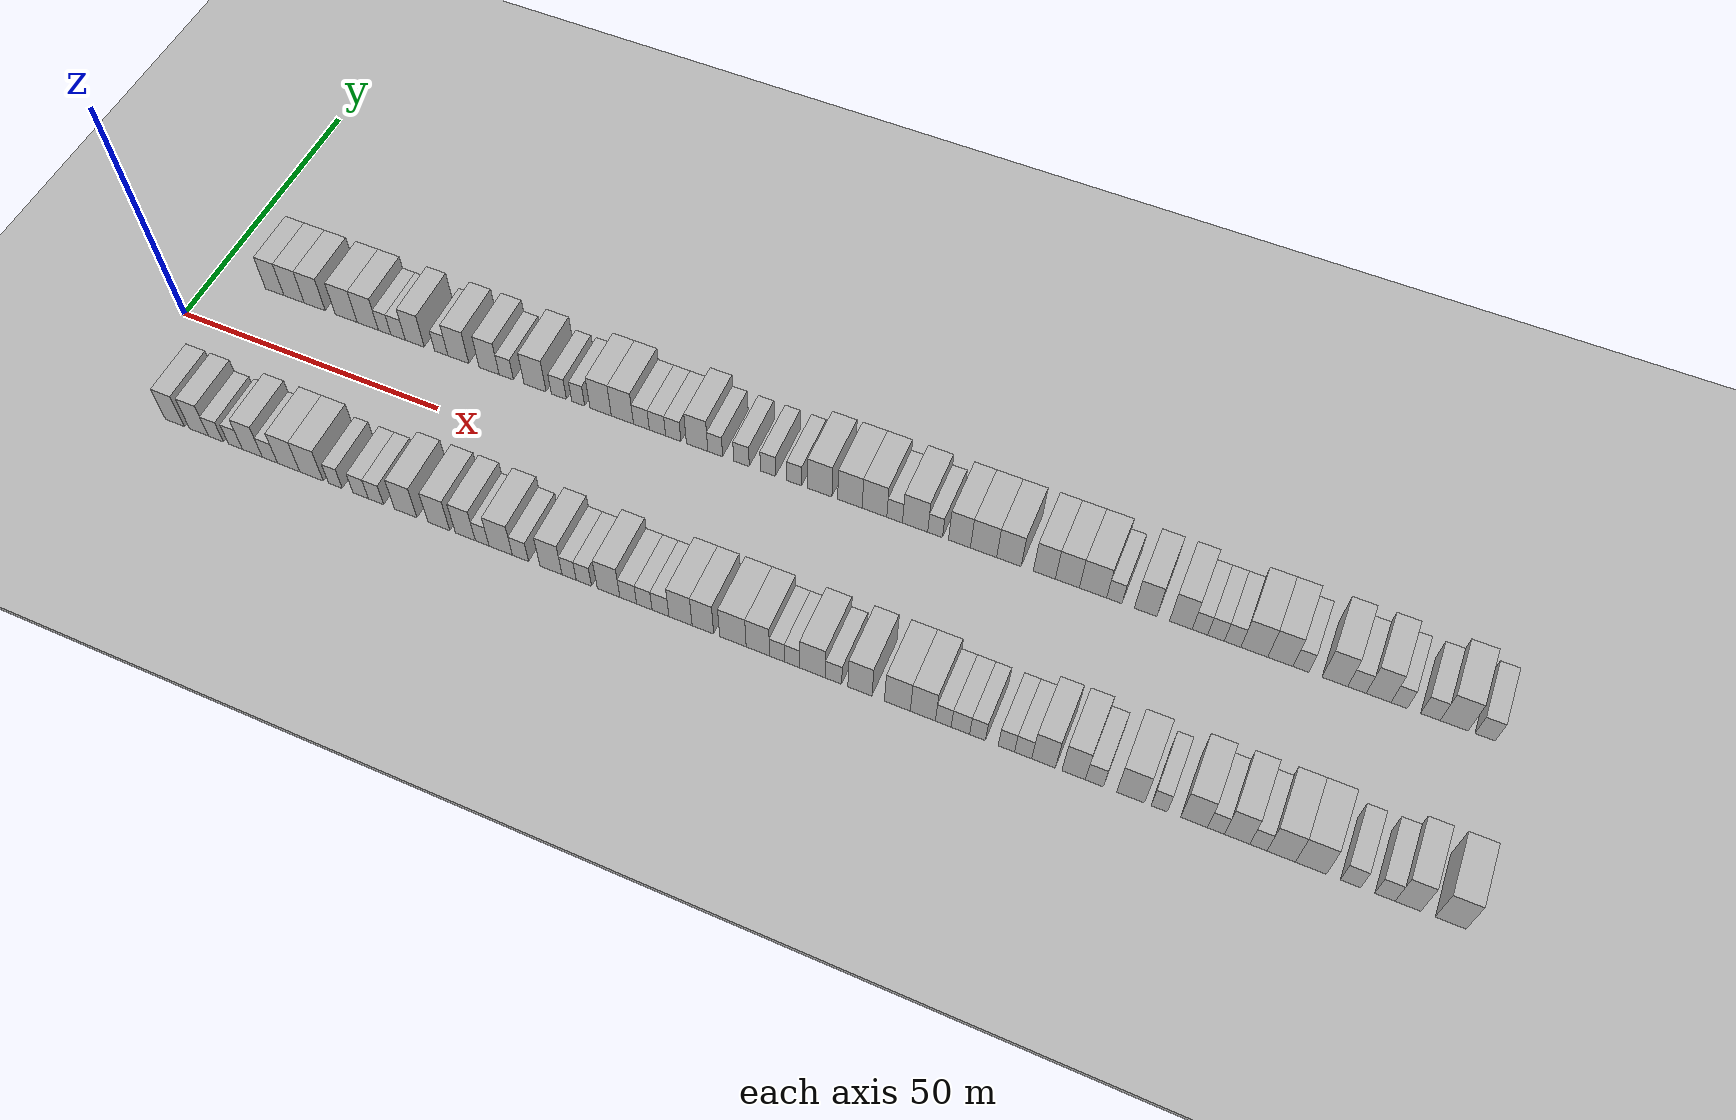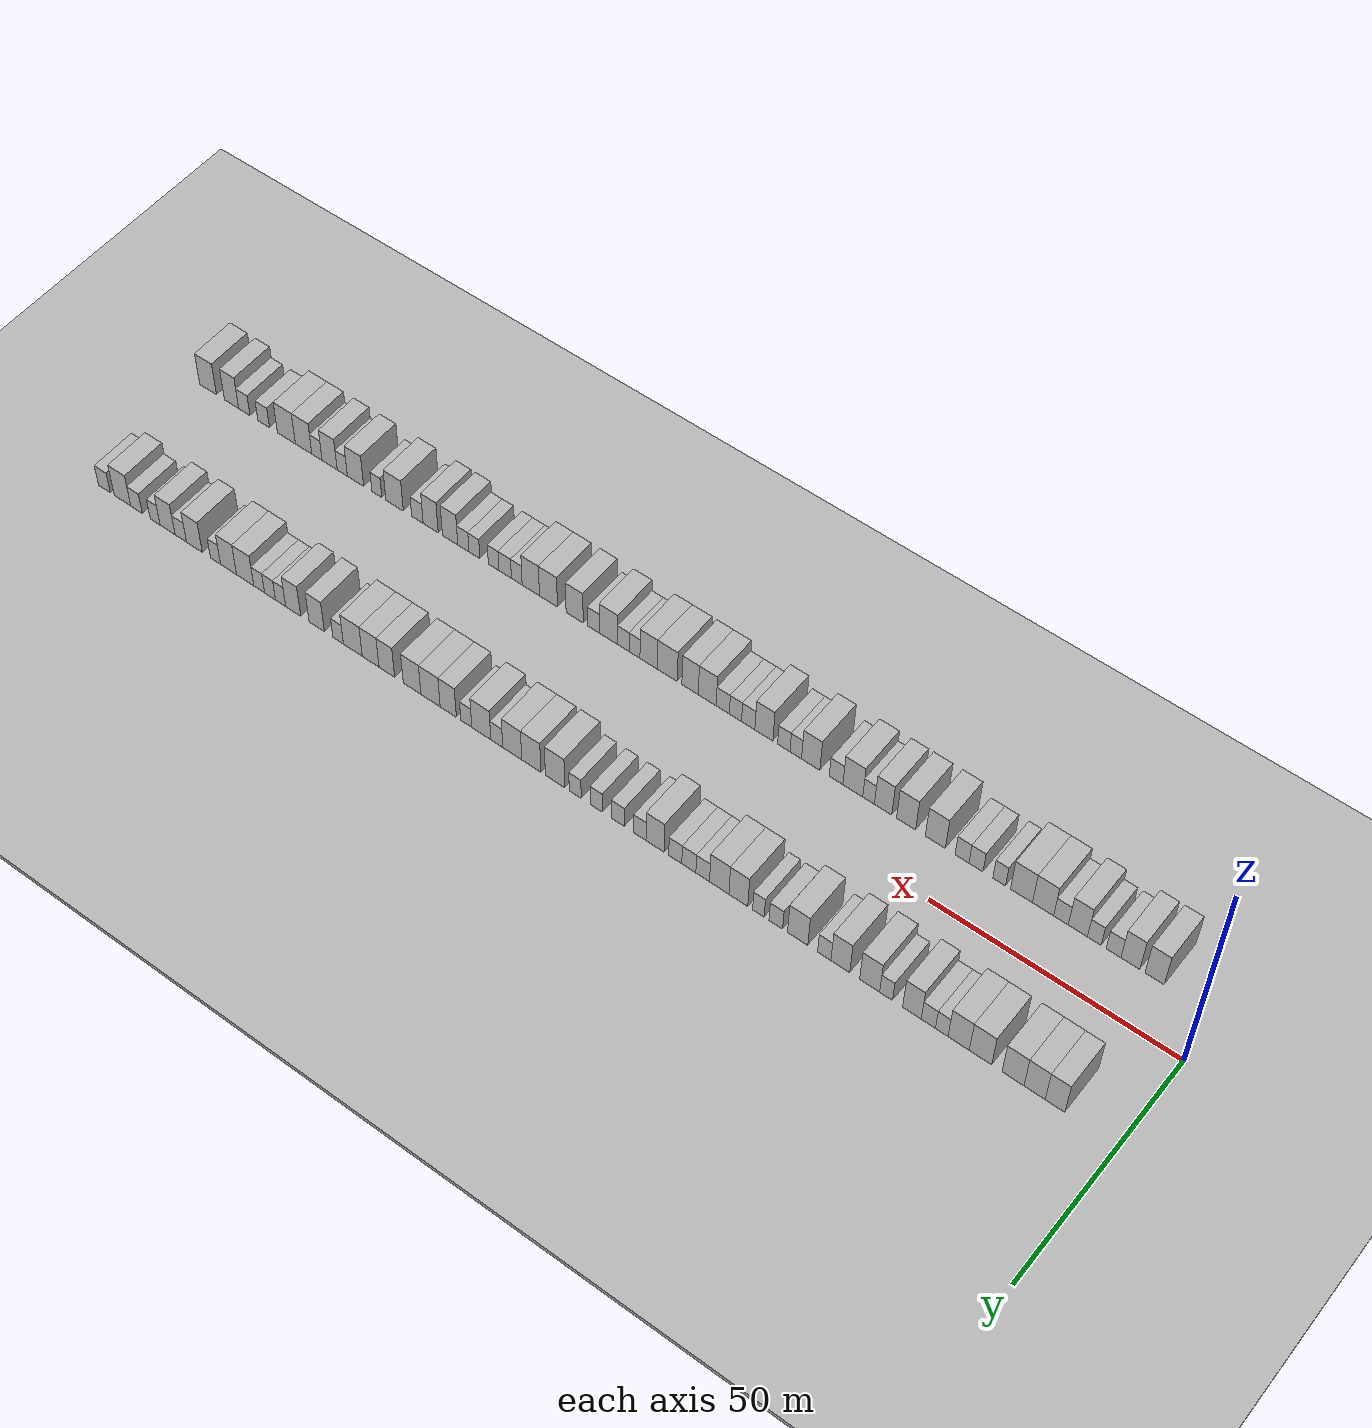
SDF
<?xml version="1.0" encoding="utf-8"?>

<sdf version="1.6">

   <world name="default">

      <gui fullscreen="0">

         <camera name="user_camera">

            <pose>-15 0 4.57585 0 0 0</pose>

            <view_controller>orbit</view_controller>

         </camera>

      </gui>

      <scene>

         <sky>

           <clouds>

             <speed>12</speed>

           </clouds>

         </sky>

         <ambient>0.4 0.4 0.4 1</ambient>

         <background>0.7 0.7 0.7 1</background>

         <shadows>1</shadows>

      </scene>

      <gravity>0 0 -9.8066</gravity>

      <magnetic_field>6e-06 2.3e-05 -4.2e-05</magnetic_field>

      <physics default="0" name="default_physics" type="ode">

         <ode>

            <solver>

               <type>quick</type>

               <iters>10</iters>

               <sor>1.0</sor>

               <use_dynamic_moi_rescaling>0</use_dynamic_moi_rescaling>

            </solver>

            <constraints>

               <cfm>0</cfm>

               <erp>0.2</erp>

               <contact_max_correcting_vel>100</contact_max_correcting_vel>

               <contact_surface_layer>0.001</contact_surface_layer>

            </constraints>

         </ode>

         <max_step_size>0.004</max_step_size>

         <real_time_factor>1</real_time_factor>

         <real_time_update_rate>250</real_time_update_rate>

      </physics>

      <light name="sun" type="directional">

         <cast_shadows>1</cast_shadows>

         <pose>0 0 10 0 0 0</pose>

         <diffuse>0.8 0.8 0.8 1</diffuse>

         <specular>0.2 0.2 0.2 1</specular>

         <attenuation>

            <range>1000</range>

            <constant>0.9</constant>

            <linear>0.01</linear>

            <quadratic>0.001</quadratic>

         </attenuation>

         <direction>-0.5 0.1 -0.9</direction>

      </light>

      <include>

         <name>ground_plane_1</name>

         <uri>model://HANNAS_ground_plane</uri>

         <pose>0 0 0  0 0 0</pose>

      </include>

      <include>

         <name>ground_plane_2</name>

         <uri>model://HANNAS_ground_plane</uri>

         <pose>100 0 0  0 0 0</pose>

      </include>

      <model name="building_1">

         <static>1</static>

         <pose frame="">11.8743 15.0000 0 0.000000 0.000000 1.570796</pose>

         <link name="link">

            <pose frame="">0 0 4.50 0 0 0</pose>

            <collision name="collision">

               <geometry>

                  <box>

                     <size>10.0000 3.7485 9.0000</size>

                  </box>

               </geometry>

               <max_contacts>10</max_contacts>

               <surface>

                  <contact>

                     <ode/>

                  </contact>

                  <bounce/>

                  <friction>

                     <torsional>

                        <ode/>

                     </torsional>

                     <ode/>

                  </friction>

               </surface>

            </collision>

            <visual name="visual">

               <cast_shadows>0</cast_shadows>

               <geometry>

                  <box>

                     <size>10.0000 3.7485 9.0000</size>

                  </box>

               </geometry>

               <material>

                  <script>

                     <uri>model://HANNAS_wall/materials/scripts</uri>

                     <uri>model://HANNAS_wall/materials/textures</uri>

                     <name>vrc/HANNAS_wall</name>

                  </script>

               </material>

            </visual>

            <self_collide>0</self_collide>

            <enable_wind>0</enable_wind>

            <kinematic>0</kinematic>

         </link>

      </model>

      <model name="building_2">

         <static>1</static>

         <pose frame="">15.7916 15.0000 0 0.000000 0.000000 1.570796</pose>

         <link name="link">

            <pose frame="">0 0 4.50 0 0 0</pose>

            <collision name="collision">

               <geometry>

                  <box>

                     <size>10.0000 4.0861 9.0000</size>

                  </box>

               </geometry>

               <max_contacts>10</max_contacts>

               <surface>

                  <contact>

                     <ode/>

                  </contact>

                  <bounce/>

                  <friction>

                     <torsional>

                        <ode/>

                     </torsional>

                     <ode/>

                  </friction>

               </surface>

            </collision>

            <visual name="visual">

               <cast_shadows>0</cast_shadows>

               <geometry>

                  <box>

                     <size>10.0000 4.0861 9.0000</size>

                  </box>

               </geometry>

               <material>

                  <script>

                     <uri>model://HANNAS_wall/materials/scripts</uri>

                     <uri>model://HANNAS_wall/materials/textures</uri>

                     <name>vrc/HANNAS_wall</name>

                  </script>

               </material>

            </visual>

            <self_collide>0</self_collide>

            <enable_wind>0</enable_wind>

            <kinematic>0</kinematic>

         </link>

      </model>

      <model name="building_3">

         <static>1</static>

         <pose frame="">19.9500 15.0000 0 0.000000 0.000000 1.570796</pose>

         <link name="link">

            <pose frame="">0 0 4.50 0 0 0</pose>

            <collision name="collision">

               <geometry>

                  <box>

                     <size>10.0000 4.2307 9.0000</size>

                  </box>

               </geometry>

               <max_contacts>10</max_contacts>

               <surface>

                  <contact>

                     <ode/>

                  </contact>

                  <bounce/>

                  <friction>

                     <torsional>

                        <ode/>

                     </torsional>

                     <ode/>

                  </friction>

               </surface>

            </collision>

            <visual name="visual">

               <cast_shadows>0</cast_shadows>

               <geometry>

                  <box>

                     <size>10.0000 4.2307 9.0000</size>

                  </box>

               </geometry>

               <material>

                  <script>

                     <uri>model://HANNAS_wall/materials/scripts</uri>

                     <uri>model://HANNAS_wall/materials/textures</uri>

                     <name>vrc/HANNAS_wall</name>

                  </script>

               </material>

            </visual>

            <self_collide>0</self_collide>

            <enable_wind>0</enable_wind>

            <kinematic>0</kinematic>

         </link>

      </model>

      <model name="building_4">

         <static>1</static>

         <pose frame="">26.2549 15.0000 0 0.000000 0.000000 1.570796</pose>

         <link name="link">

            <pose frame="">0 0 4.50 0 0 0</pose>

            <collision name="collision">

               <geometry>

                  <box>

                     <size>10.0000 4.3791 9.0000</size>

                  </box>

               </geometry>

               <max_contacts>10</max_contacts>

               <surface>

                  <contact>

                     <ode/>

                  </contact>

                  <bounce/>

                  <friction>

                     <torsional>

                        <ode/>

                     </torsional>

                     <ode/>

                  </friction>

               </surface>

            </collision>

            <visual name="visual">

               <cast_shadows>0</cast_shadows>

               <geometry>

                  <box>

                     <size>10.0000 4.3791 9.0000</size>

                  </box>

               </geometry>

               <material>

                  <script>

                     <uri>model://HANNAS_wall/materials/scripts</uri>

                     <uri>model://HANNAS_wall/materials/textures</uri>

                     <name>vrc/HANNAS_wall</name>

                  </script>

               </material>

            </visual>

            <self_collide>0</self_collide>

            <enable_wind>0</enable_wind>

            <kinematic>0</kinematic>

         </link>

      </model>

      <model name="building_5">

         <static>1</static>

         <pose frame="">30.5329 15.0000 0 0.000000 0.000000 1.570796</pose>

         <link name="link">

            <pose frame="">0 0 4.50 0 0 0</pose>

            <collision name="collision">

               <geometry>

                  <box>

                     <size>10.0000 4.1769 9.0000</size>

                  </box>

               </geometry>

               <max_contacts>10</max_contacts>

               <surface>

                  <contact>

                     <ode/>

                  </contact>

                  <bounce/>

                  <friction>

                     <torsional>

                        <ode/>

                     </torsional>

                     <ode/>

                  </friction>

               </surface>

            </collision>

            <visual name="visual">

               <cast_shadows>0</cast_shadows>

               <geometry>

                  <box>

                     <size>10.0000 4.1769 9.0000</size>

                  </box>

               </geometry>

               <material>

                  <script>

                     <uri>model://HANNAS_wall/materials/scripts</uri>

                     <uri>model://HANNAS_wall/materials/textures</uri>

                     <name>vrc/HANNAS_wall</name>

                  </script>

               </material>

            </visual>

            <self_collide>0</self_collide>

            <enable_wind>0</enable_wind>

            <kinematic>0</kinematic>

         </link>

      </model>

      <model name="building_6">

         <static>1</static>

         <pose frame="">33.8588 15.0000 0 0.000000 0.000000 1.570796</pose>

         <link name="link">

            <pose frame="">0 0 3.00 0 0 0</pose>

            <collision name="collision">

               <geometry>

                  <box>

                     <size>10.0000 2.4749 6.0000</size>

                  </box>

               </geometry>

               <max_contacts>10</max_contacts>

               <surface>

                  <contact>

                     <ode/>

                  </contact>

                  <bounce/>

                  <friction>

                     <torsional>

                        <ode/>

                     </torsional>

                     <ode/>

                  </friction>

               </surface>

            </collision>

            <visual name="visual">

               <cast_shadows>0</cast_shadows>

               <geometry>

                  <box>

                     <size>10.0000 2.4749 6.0000</size>

                  </box>

               </geometry>

               <material>

                  <script>

                     <uri>model://HANNAS_wall/materials/scripts</uri>

                     <uri>model://HANNAS_wall/materials/textures</uri>

                     <name>vrc/HANNAS_wall</name>

                  </script>

               </material>

            </visual>

            <self_collide>0</self_collide>

            <enable_wind>0</enable_wind>

            <kinematic>0</kinematic>

         </link>

      </model>

      <model name="building_7">

         <static>1</static>

         <pose frame="">36.5099 15.0000 0 0.000000 0.000000 1.570796</pose>

         <link name="link">

            <pose frame="">0 0 3.00 0 0 0</pose>

            <collision name="collision">

               <geometry>

                  <box>

                     <size>10.0000 2.8275 6.0000</size>

                  </box>

               </geometry>

               <max_contacts>10</max_contacts>

               <surface>

                  <contact>

                     <ode/>

                  </contact>

                  <bounce/>

                  <friction>

                     <torsional>

                        <ode/>

                     </torsional>

                     <ode/>

                  </friction>

               </surface>

            </collision>

            <visual name="visual">

               <cast_shadows>0</cast_shadows>

               <geometry>

                  <box>

                     <size>10.0000 2.8275 6.0000</size>

                  </box>

               </geometry>

               <material>

                  <script>

                     <uri>model://HANNAS_wall/materials/scripts</uri>

                     <uri>model://HANNAS_wall/materials/textures</uri>

                     <name>vrc/HANNAS_wall</name>

                  </script>

               </material>

            </visual>

            <self_collide>0</self_collide>

            <enable_wind>0</enable_wind>

            <kinematic>0</kinematic>

         </link>

      </model>

      <model name="building_8">

         <static>1</static>

         <pose frame="">39.7782 15.0000 0 0.000000 0.000000 1.570796</pose>

         <link name="link">

            <pose frame="">0 0 4.50 0 0 0</pose>

            <collision name="collision">

               <geometry>

                  <box>

                     <size>10.0000 3.7091 9.0000</size>

                  </box>

               </geometry>

               <max_contacts>10</max_contacts>

               <surface>

                  <contact>

                     <ode/>

                  </contact>

                  <bounce/>

                  <friction>

                     <torsional>

                        <ode/>

                     </torsional>

                     <ode/>

                  </friction>

               </surface>

            </collision>

            <visual name="visual">

               <cast_shadows>0</cast_shadows>

               <geometry>

                  <box>

                     <size>10.0000 3.7091 9.0000</size>

                  </box>

               </geometry>

               <material>

                  <script>

                     <uri>model://HANNAS_wall/materials/scripts</uri>

                     <uri>model://HANNAS_wall/materials/textures</uri>

                     <name>vrc/HANNAS_wall</name>

                  </script>

               </material>

            </visual>

            <self_collide>0</self_collide>

            <enable_wind>0</enable_wind>

            <kinematic>0</kinematic>

         </link>

      </model>

      <model name="building_9">

         <static>1</static>

         <pose frame="">44.9292 15.0000 0 0.000000 0.000000 1.570796</pose>

         <link name="link">

            <pose frame="">0 0 3.00 0 0 0</pose>

            <collision name="collision">

               <geometry>

                  <box>

                     <size>10.0000 2.5927 6.0000</size>

                  </box>

               </geometry>

               <max_contacts>10</max_contacts>

               <surface>

                  <contact>

                     <ode/>

                  </contact>

                  <bounce/>

                  <friction>

                     <torsional>

                        <ode/>

                     </torsional>

                     <ode/>

                  </friction>

               </surface>

            </collision>

            <visual name="visual">

               <cast_shadows>0</cast_shadows>

               <geometry>

                  <box>

                     <size>10.0000 2.5927 6.0000</size>

                  </box>

               </geometry>

               <material>

                  <script>

                     <uri>model://HANNAS_wall/materials/scripts</uri>

                     <uri>model://HANNAS_wall/materials/textures</uri>

                     <name>vrc/HANNAS_wall</name>

                  </script>

               </material>

            </visual>

            <self_collide>0</self_collide>

            <enable_wind>0</enable_wind>

            <kinematic>0</kinematic>

         </link>

      </model>

      <model name="building_10">

         <static>1</static>

         <pose frame="">48.2375 15.0000 0 0.000000 0.000000 1.570796</pose>

         <link name="link">

            <pose frame="">0 0 4.50 0 0 0</pose>

            <collision name="collision">

               <geometry>

                  <box>

                     <size>10.0000 4.0239 9.0000</size>

                  </box>

               </geometry>

               <max_contacts>10</max_contacts>

               <surface>

                  <contact>

                     <ode/>

                  </contact>

                  <bounce/>

                  <friction>

                     <torsional>

                        <ode/>

                     </torsional>

                     <ode/>

                  </friction>

               </surface>

            </collision>

            <visual name="visual">

               <cast_shadows>0</cast_shadows>

               <geometry>

                  <box>

                     <size>10.0000 4.0239 9.0000</size>

                  </box>

               </geometry>

               <material>

                  <script>

                     <uri>model://HANNAS_wall/materials/scripts</uri>

                     <uri>model://HANNAS_wall/materials/textures</uri>

                     <name>vrc/HANNAS_wall</name>

                  </script>

               </material>

            </visual>

            <self_collide>0</self_collide>

            <enable_wind>0</enable_wind>

            <kinematic>0</kinematic>

         </link>

      </model>

      <model name="building_11">

         <static>1</static>

         <pose frame="">54.1597 15.0000 0 0.000000 0.000000 1.570796</pose>

         <link name="link">

            <pose frame="">0 0 4.50 0 0 0</pose>

            <collision name="collision">

               <geometry>

                  <box>

                     <size>10.0000 3.8205 9.0000</size>

                  </box>

               </geometry>

               <max_contacts>10</max_contacts>

               <surface>

                  <contact>

                     <ode/>

                  </contact>

                  <bounce/>

                  <friction>

                     <torsional>

                        <ode/>

                     </torsional>

                     <ode/>

                  </friction>

               </surface>

            </collision>

            <visual name="visual">

               <cast_shadows>0</cast_shadows>

               <geometry>

                  <box>

                     <size>10.0000 3.8205 9.0000</size>

                  </box>

               </geometry>

               <material>

                  <script>

                     <uri>model://HANNAS_wall/materials/scripts</uri>

                     <uri>model://HANNAS_wall/materials/textures</uri>

                     <name>vrc/HANNAS_wall</name>

                  </script>

               </material>

            </visual>

            <self_collide>0</self_collide>

            <enable_wind>0</enable_wind>

            <kinematic>0</kinematic>

         </link>

      </model>

      <model name="building_12">

         <static>1</static>

         <pose frame="">57.4333 15.0000 0 0.000000 0.000000 1.570796</pose>

         <link name="link">

            <pose frame="">0 0 3.00 0 0 0</pose>

            <collision name="collision">

               <geometry>

                  <box>

                     <size>10.0000 2.7268 6.0000</size>

                  </box>

               </geometry>

               <max_contacts>10</max_contacts>

               <surface>

                  <contact>

                     <ode/>

                  </contact>

                  <bounce/>

                  <friction>

                     <torsional>

                        <ode/>

                     </torsional>

                     <ode/>

                  </friction>

               </surface>

            </collision>

            <visual name="visual">

               <cast_shadows>0</cast_shadows>

               <geometry>

                  <box>

                     <size>10.0000 2.7268 6.0000</size>

                  </box>

               </geometry>

               <material>

                  <script>

                     <uri>model://HANNAS_wall/materials/scripts</uri>

                     <uri>model://HANNAS_wall/materials/textures</uri>

                     <name>vrc/HANNAS_wall</name>

                  </script>

               </material>

            </visual>

            <self_collide>0</self_collide>

            <enable_wind>0</enable_wind>

            <kinematic>0</kinematic>

         </link>

      </model>

      <model name="building_13">

         <static>1</static>

         <pose frame="">62.8809 15.0000 0 0.000000 0.000000 1.570796</pose>

         <link name="link">

            <pose frame="">0 0 4.50 0 0 0</pose>

            <collision name="collision">

               <geometry>

                  <box>

                     <size>10.0000 4.1684 9.0000</size>

                  </box>

               </geometry>

               <max_contacts>10</max_contacts>

               <surface>

                  <contact>

                     <ode/>

                  </contact>

                  <bounce/>

                  <friction>

                     <torsional>

                        <ode/>

                     </torsional>

                     <ode/>

                  </friction>

               </surface>

            </collision>

            <visual name="visual">

               <cast_shadows>0</cast_shadows>

               <geometry>

                  <box>

                     <size>10.0000 4.1684 9.0000</size>

                  </box>

               </geometry>

               <material>

                  <script>

                     <uri>model://HANNAS_wall/materials/scripts</uri>

                     <uri>model://HANNAS_wall/materials/textures</uri>

                     <name>vrc/HANNAS_wall</name>

                  </script>

               </material>

            </visual>

            <self_collide>0</self_collide>

            <enable_wind>0</enable_wind>

            <kinematic>0</kinematic>

         </link>

      </model>

      <model name="building_14">

         <static>1</static>

         <pose frame="">67.3798 15.0000 0 0.000000 0.000000 1.570796</pose>

         <link name="link">

            <pose frame="">0 0 3.00 0 0 0</pose>

            <collision name="collision">

               <geometry>

                  <box>

                     <size>10.0000 2.8293 6.0000</size>

                  </box>

               </geometry>

               <max_contacts>10</max_contacts>

               <surface>

                  <contact>

                     <ode/>

                  </contact>

                  <bounce/>

                  <friction>

                     <torsional>

                        <ode/>

                     </torsional>

                     <ode/>

                  </friction>

               </surface>

            </collision>

            <visual name="visual">

               <cast_shadows>0</cast_shadows>

               <geometry>

                  <box>

                     <size>10.0000 2.8293 6.0000</size>

                  </box>

               </geometry>

               <material>

                  <script>

                     <uri>model://HANNAS_wall/materials/scripts</uri>

                     <uri>model://HANNAS_wall/materials/textures</uri>

                     <name>vrc/HANNAS_wall</name>

                  </script>

               </material>

            </visual>

            <self_collide>0</self_collide>

            <enable_wind>0</enable_wind>

            <kinematic>0</kinematic>

         </link>

      </model>

      <model name="building_15">

         <static>1</static>

         <pose frame="">70.9947 15.0000 0 0.000000 0.000000 1.570796</pose>

         <link name="link">

            <pose frame="">0 0 3.00 0 0 0</pose>

            <collision name="collision">

               <geometry>

                  <box>

                     <size>10.0000 2.4004 6.0000</size>

                  </box>

               </geometry>

               <max_contacts>10</max_contacts>

               <surface>

                  <contact>

                     <ode/>

                  </contact>

                  <bounce/>

                  <friction>

                     <torsional>

                        <ode/>

                     </torsional>

                     <ode/>

                  </friction>

               </surface>

            </collision>

            <visual name="visual">

               <cast_shadows>0</cast_shadows>

               <geometry>

                  <box>

                     <size>10.0000 2.4004 6.0000</size>

                  </box>

               </geometry>

               <material>

                  <script>

                     <uri>model://HANNAS_wall/materials/scripts</uri>

                     <uri>model://HANNAS_wall/materials/textures</uri>

                     <name>vrc/HANNAS_wall</name>

                  </script>

               </material>

            </visual>

            <self_collide>0</self_collide>

            <enable_wind>0</enable_wind>

            <kinematic>0</kinematic>

         </link>

      </model>

      <model name="building_16">

         <static>1</static>

         <pose frame="">75.1674 15.0000 0 0.000000 0.000000 1.570796</pose>

         <link name="link">

            <pose frame="">0 0 4.50 0 0 0</pose>

            <collision name="collision">

               <geometry>

                  <box>

                     <size>10.0000 3.9452 9.0000</size>

                  </box>

               </geometry>

               <max_contacts>10</max_contacts>

               <surface>

                  <contact>

                     <ode/>

                  </contact>

                  <bounce/>

                  <friction>

                     <torsional>

                        <ode/>

                     </torsional>

                     <ode/>

                  </friction>

               </surface>

            </collision>

            <visual name="visual">

               <cast_shadows>0</cast_shadows>

               <geometry>

                  <box>

                     <size>10.0000 3.9452 9.0000</size>

                  </box>

               </geometry>

               <material>

                  <script>

                     <uri>model://HANNAS_wall/materials/scripts</uri>

                     <uri>model://HANNAS_wall/materials/textures</uri>

                     <name>vrc/HANNAS_wall</name>

                  </script>

               </material>

            </visual>

            <self_collide>0</self_collide>

            <enable_wind>0</enable_wind>

            <kinematic>0</kinematic>

         </link>

      </model>

      <model name="building_17">

         <static>1</static>

         <pose frame="">79.1817 15.0000 0 0.000000 0.000000 1.570796</pose>

         <link name="link">

            <pose frame="">0 0 4.50 0 0 0</pose>

            <collision name="collision">

               <geometry>

                  <box>

                     <size>10.0000 4.0834 9.0000</size>

                  </box>

               </geometry>

               <max_contacts>10</max_contacts>

               <surface>

                  <contact>

                     <ode/>

                  </contact>

                  <bounce/>

                  <friction>

                     <torsional>

                        <ode/>

                     </torsional>

                     <ode/>

                  </friction>

               </surface>

            </collision>

            <visual name="visual">

               <cast_shadows>0</cast_shadows>

               <geometry>

                  <box>

                     <size>10.0000 4.0834 9.0000</size>

                  </box>

               </geometry>

               <material>

                  <script>

                     <uri>model://HANNAS_wall/materials/scripts</uri>

                     <uri>model://HANNAS_wall/materials/textures</uri>

                     <name>vrc/HANNAS_wall</name>

                  </script>

               </material>

            </visual>

            <self_collide>0</self_collide>

            <enable_wind>0</enable_wind>

            <kinematic>0</kinematic>

         </link>

      </model>

      <model name="building_18">

         <static>1</static>

         <pose frame="">82.6705 15.0000 0 0.000000 0.000000 1.570796</pose>

         <link name="link">

            <pose frame="">0 0 3.00 0 0 0</pose>

            <collision name="collision">

               <geometry>

                  <box>

                     <size>10.0000 2.8942 6.0000</size>

                  </box>

               </geometry>

               <max_contacts>10</max_contacts>

               <surface>

                  <contact>

                     <ode/>

                  </contact>

                  <bounce/>

                  <friction>

                     <torsional>

                        <ode/>

                     </torsional>

                     <ode/>

                  </friction>

               </surface>

            </collision>

            <visual name="visual">

               <cast_shadows>0</cast_shadows>

               <geometry>

                  <box>

                     <size>10.0000 2.8942 6.0000</size>

                  </box>

               </geometry>

               <material>

                  <script>

                     <uri>model://HANNAS_wall/materials/scripts</uri>

                     <uri>model://HANNAS_wall/materials/textures</uri>

                     <name>vrc/HANNAS_wall</name>

                  </script>

               </material>

            </visual>

            <self_collide>0</self_collide>

            <enable_wind>0</enable_wind>

            <kinematic>0</kinematic>

         </link>

      </model>

      <model name="building_19">

         <static>1</static>

         <pose frame="">85.6084 15.0000 0 0.000000 0.000000 1.570796</pose>

         <link name="link">

            <pose frame="">0 0 3.00 0 0 0</pose>

            <collision name="collision">

               <geometry>

                  <box>

                     <size>10.0000 2.9817 6.0000</size>

                  </box>

               </geometry>

               <max_contacts>10</max_contacts>

               <surface>

                  <contact>

                     <ode/>

                  </contact>

                  <bounce/>

                  <friction>

                     <torsional>

                        <ode/>

                     </torsional>

                     <ode/>

                  </friction>

               </surface>

            </collision>

            <visual name="visual">

               <cast_shadows>0</cast_shadows>

               <geometry>

                  <box>

                     <size>10.0000 2.9817 6.0000</size>

                  </box>

               </geometry>

               <material>

                  <script>

                     <uri>model://HANNAS_wall/materials/scripts</uri>

                     <uri>model://HANNAS_wall/materials/textures</uri>

                     <name>vrc/HANNAS_wall</name>

                  </script>

               </material>

            </visual>

            <self_collide>0</self_collide>

            <enable_wind>0</enable_wind>

            <kinematic>0</kinematic>

         </link>

      </model>

      <model name="building_20">

         <static>1</static>

         <pose frame="">88.4929 15.0000 0 0.000000 0.000000 1.570796</pose>

         <link name="link">

            <pose frame="">0 0 3.00 0 0 0</pose>

            <collision name="collision">

               <geometry>

                  <box>

                     <size>10.0000 2.7872 6.0000</size>

                  </box>

               </geometry>

               <max_contacts>10</max_contacts>

               <surface>

                  <contact>

                     <ode/>

                  </contact>

                  <bounce/>

                  <friction>

                     <torsional>

                        <ode/>

                     </torsional>

                     <ode/>

                  </friction>

               </surface>

            </collision>

            <visual name="visual">

               <cast_shadows>0</cast_shadows>

               <geometry>

                  <box>

                     <size>10.0000 2.7872 6.0000</size>

                  </box>

               </geometry>

               <material>

                  <script>

                     <uri>model://HANNAS_wall/materials/scripts</uri>

                     <uri>model://HANNAS_wall/materials/textures</uri>

                     <name>vrc/HANNAS_wall</name>

                  </script>

               </material>

            </visual>

            <self_collide>0</self_collide>

            <enable_wind>0</enable_wind>

            <kinematic>0</kinematic>

         </link>

      </model>

      <model name="building_21">

         <static>1</static>

         <pose frame="">92.8238 15.0000 0 0.000000 0.000000 1.570796</pose>

         <link name="link">

            <pose frame="">0 0 4.50 0 0 0</pose>

            <collision name="collision">

               <geometry>

                  <box>

                     <size>10.0000 3.8746 9.0000</size>

                  </box>

               </geometry>

               <max_contacts>10</max_contacts>

               <surface>

                  <contact>

                     <ode/>

                  </contact>

                  <bounce/>

                  <friction>

                     <torsional>

                        <ode/>

                     </torsional>

                     <ode/>

                  </friction>

               </surface>

            </collision>

            <visual name="visual">

               <cast_shadows>0</cast_shadows>

               <geometry>

                  <box>

                     <size>10.0000 3.8746 9.0000</size>

                  </box>

               </geometry>

               <material>

                  <script>

                     <uri>model://HANNAS_wall/materials/scripts</uri>

                     <uri>model://HANNAS_wall/materials/textures</uri>

                     <name>vrc/HANNAS_wall</name>

                  </script>

               </material>

            </visual>

            <self_collide>0</self_collide>

            <enable_wind>0</enable_wind>

            <kinematic>0</kinematic>

         </link>

      </model>

      <model name="building_22">

         <static>1</static>

         <pose frame="">96.0821 15.0000 0 0.000000 0.000000 1.570796</pose>

         <link name="link">

            <pose frame="">0 0 3.00 0 0 0</pose>

            <collision name="collision">

               <geometry>

                  <box>

                     <size>10.0000 2.6420 6.0000</size>

                  </box>

               </geometry>

               <max_contacts>10</max_contacts>

               <surface>

                  <contact>

                     <ode/>

                  </contact>

                  <bounce/>

                  <friction>

                     <torsional>

                        <ode/>

                     </torsional>

                     <ode/>

                  </friction>

               </surface>

            </collision>

            <visual name="visual">

               <cast_shadows>0</cast_shadows>

               <geometry>

                  <box>

                     <size>10.0000 2.6420 6.0000</size>

                  </box>

               </geometry>

               <material>

                  <script>

                     <uri>model://HANNAS_wall/materials/scripts</uri>

                     <uri>model://HANNAS_wall/materials/textures</uri>

                     <name>vrc/HANNAS_wall</name>

                  </script>

               </material>

            </visual>

            <self_collide>0</self_collide>

            <enable_wind>0</enable_wind>

            <kinematic>0</kinematic>

         </link>

      </model>

      <model name="building_23">

         <static>1</static>

         <pose frame="">100.7850 15.0000 0 0.000000 0.000000 1.570796</pose>

         <link name="link">

            <pose frame="">0 0 3.00 0 0 0</pose>

            <collision name="collision">

               <geometry>

                  <box>

                     <size>10.0000 2.7638 6.0000</size>

                  </box>

               </geometry>

               <max_contacts>10</max_contacts>

               <surface>

                  <contact>

                     <ode/>

                  </contact>

                  <bounce/>

                  <friction>

                     <torsional>

                        <ode/>

                     </torsional>

                     <ode/>

                  </friction>

               </surface>

            </collision>

            <visual name="visual">

               <cast_shadows>0</cast_shadows>

               <geometry>

                  <box>

                     <size>10.0000 2.7638 6.0000</size>

                  </box>

               </geometry>

               <material>

                  <script>

                     <uri>model://HANNAS_wall/materials/scripts</uri>

                     <uri>model://HANNAS_wall/materials/textures</uri>

                     <name>vrc/HANNAS_wall</name>

                  </script>

               </material>

            </visual>

            <self_collide>0</self_collide>

            <enable_wind>0</enable_wind>

            <kinematic>0</kinematic>

         </link>

      </model>

      <model name="building_24">

         <static>1</static>

         <pose frame="">105.5017 15.0000 0 0.000000 0.000000 1.570796</pose>

         <link name="link">

            <pose frame="">0 0 3.00 0 0 0</pose>

            <collision name="collision">

               <geometry>

                  <box>

                     <size>10.0000 2.6697 6.0000</size>

                  </box>

               </geometry>

               <max_contacts>10</max_contacts>

               <surface>

                  <contact>

                     <ode/>

                  </contact>

                  <bounce/>

                  <friction>

                     <torsional>

                        <ode/>

                     </torsional>

                     <ode/>

                  </friction>

               </surface>

            </collision>

            <visual name="visual">

               <cast_shadows>0</cast_shadows>

               <geometry>

                  <box>

                     <size>10.0000 2.6697 6.0000</size>

                  </box>

               </geometry>

               <material>

                  <script>

                     <uri>model://HANNAS_wall/materials/scripts</uri>

                     <uri>model://HANNAS_wall/materials/textures</uri>

                     <name>vrc/HANNAS_wall</name>

                  </script>

               </material>

            </visual>

            <self_collide>0</self_collide>

            <enable_wind>0</enable_wind>

            <kinematic>0</kinematic>

         </link>

      </model>

      <model name="building_25">

         <static>1</static>

         <pose frame="">110.1485 15.0000 0 0.000000 0.000000 1.570796</pose>

         <link name="link">

            <pose frame="">0 0 3.00 0 0 0</pose>

            <collision name="collision">

               <geometry>

                  <box>

                     <size>10.0000 2.6238 6.0000</size>

                  </box>

               </geometry>

               <max_contacts>10</max_contacts>

               <surface>

                  <contact>

                     <ode/>

                  </contact>

                  <bounce/>

                  <friction>

                     <torsional>

                        <ode/>

                     </torsional>

                     <ode/>

                  </friction>

               </surface>

            </collision>

            <visual name="visual">

               <cast_shadows>0</cast_shadows>

               <geometry>

                  <box>

                     <size>10.0000 2.6238 6.0000</size>

                  </box>

               </geometry>

               <material>

                  <script>

                     <uri>model://HANNAS_wall/materials/scripts</uri>

                     <uri>model://HANNAS_wall/materials/textures</uri>

                     <name>vrc/HANNAS_wall</name>

                  </script>

               </material>

            </visual>

            <self_collide>0</self_collide>

            <enable_wind>0</enable_wind>

            <kinematic>0</kinematic>

         </link>

      </model>

      <model name="building_26">

         <static>1</static>

         <pose frame="">114.5944 15.0000 0 0.000000 0.000000 1.570796</pose>

         <link name="link">

            <pose frame="">0 0 4.50 0 0 0</pose>

            <collision name="collision">

               <geometry>

                  <box>

                     <size>10.0000 4.2680 9.0000</size>

                  </box>

               </geometry>

               <max_contacts>10</max_contacts>

               <surface>

                  <contact>

                     <ode/>

                  </contact>

                  <bounce/>

                  <friction>

                     <torsional>

                        <ode/>

                     </torsional>

                     <ode/>

                  </friction>

               </surface>

            </collision>

            <visual name="visual">

               <cast_shadows>0</cast_shadows>

               <geometry>

                  <box>

                     <size>10.0000 4.2680 9.0000</size>

                  </box>

               </geometry>

               <material>

                  <script>

                     <uri>model://HANNAS_wall/materials/scripts</uri>

                     <uri>model://HANNAS_wall/materials/textures</uri>

                     <name>vrc/HANNAS_wall</name>

                  </script>

               </material>

            </visual>

            <self_collide>0</self_collide>

            <enable_wind>0</enable_wind>

            <kinematic>0</kinematic>

         </link>

      </model>

      <model name="building_27">

         <static>1</static>

         <pose frame="">119.8555 15.0000 0 0.000000 0.000000 1.570796</pose>

         <link name="link">

            <pose frame="">0 0 4.50 0 0 0</pose>

            <collision name="collision">

               <geometry>

                  <box>

                     <size>10.0000 4.2542 9.0000</size>

                  </box>

               </geometry>

               <max_contacts>10</max_contacts>

               <surface>

                  <contact>

                     <ode/>

                  </contact>

                  <bounce/>

                  <friction>

                     <torsional>

                        <ode/>

                     </torsional>

                     <ode/>

                  </friction>

               </surface>

            </collision>

            <visual name="visual">

               <cast_shadows>0</cast_shadows>

               <geometry>

                  <box>

                     <size>10.0000 4.2542 9.0000</size>

                  </box>

               </geometry>

               <material>

                  <script>

                     <uri>model://HANNAS_wall/materials/scripts</uri>

                     <uri>model://HANNAS_wall/materials/textures</uri>

                     <name>vrc/HANNAS_wall</name>

                  </script>

               </material>

            </visual>

            <self_collide>0</self_collide>

            <enable_wind>0</enable_wind>

            <kinematic>0</kinematic>

         </link>

      </model>

      <model name="building_28">

         <static>1</static>

         <pose frame="">124.1061 15.0000 0 0.000000 0.000000 1.570796</pose>

         <link name="link">

            <pose frame="">0 0 4.50 0 0 0</pose>

            <collision name="collision">

               <geometry>

                  <box>

                     <size>10.0000 4.2471 9.0000</size>

                  </box>

               </geometry>

               <max_contacts>10</max_contacts>

               <surface>

                  <contact>

                     <ode/>

                  </contact>

                  <bounce/>

                  <friction>

                     <torsional>

                        <ode/>

                     </torsional>

                     <ode/>

                  </friction>

               </surface>

            </collision>

            <visual name="visual">

               <cast_shadows>0</cast_shadows>

               <geometry>

                  <box>

                     <size>10.0000 4.2471 9.0000</size>

                  </box>

               </geometry>

               <material>

                  <script>

                     <uri>model://HANNAS_wall/materials/scripts</uri>

                     <uri>model://HANNAS_wall/materials/textures</uri>

                     <name>vrc/HANNAS_wall</name>

                  </script>

               </material>

            </visual>

            <self_collide>0</self_collide>

            <enable_wind>0</enable_wind>

            <kinematic>0</kinematic>

         </link>

      </model>

      <model name="building_29">

         <static>1</static>

         <pose frame="">127.5682 15.0000 0 0.000000 0.000000 1.570796</pose>

         <link name="link">

            <pose frame="">0 0 3.00 0 0 0</pose>

            <collision name="collision">

               <geometry>

                  <box>

                     <size>10.0000 2.6771 6.0000</size>

                  </box>

               </geometry>

               <max_contacts>10</max_contacts>

               <surface>

                  <contact>

                     <ode/>

                  </contact>

                  <bounce/>

                  <friction>

                     <torsional>

                        <ode/>

                     </torsional>

                     <ode/>

                  </friction>

               </surface>

            </collision>

            <visual name="visual">

               <cast_shadows>0</cast_shadows>

               <geometry>

                  <box>

                     <size>10.0000 2.6771 6.0000</size>

                  </box>

               </geometry>

               <material>

                  <script>

                     <uri>model://HANNAS_wall/materials/scripts</uri>

                     <uri>model://HANNAS_wall/materials/textures</uri>

                     <name>vrc/HANNAS_wall</name>

                  </script>

               </material>

            </visual>

            <self_collide>0</self_collide>

            <enable_wind>0</enable_wind>

            <kinematic>0</kinematic>

         </link>

      </model>

      <model name="building_30">

         <static>1</static>

         <pose frame="">131.0592 15.0000 0 0.000000 0.000000 1.570796</pose>

         <link name="link">

            <pose frame="">0 0 4.50 0 0 0</pose>

            <collision name="collision">

               <geometry>

                  <box>

                     <size>10.0000 4.3049 9.0000</size>

                  </box>

               </geometry>

               <max_contacts>10</max_contacts>

               <surface>

                  <contact>

                     <ode/>

                  </contact>

                  <bounce/>

                  <friction>

                     <torsional>

                        <ode/>

                     </torsional>

                     <ode/>

                  </friction>

               </surface>

            </collision>

            <visual name="visual">

               <cast_shadows>0</cast_shadows>

               <geometry>

                  <box>

                     <size>10.0000 4.3049 9.0000</size>

                  </box>

               </geometry>

               <material>

                  <script>

                     <uri>model://HANNAS_wall/materials/scripts</uri>

                     <uri>model://HANNAS_wall/materials/textures</uri>

                     <name>vrc/HANNAS_wall</name>

                  </script>

               </material>

            </visual>

            <self_collide>0</self_collide>

            <enable_wind>0</enable_wind>

            <kinematic>0</kinematic>

         </link>

      </model>

      <model name="building_31">

         <static>1</static>

         <pose frame="">134.4650 15.0000 0 0.000000 0.000000 1.570796</pose>

         <link name="link">

            <pose frame="">0 0 3.00 0 0 0</pose>

            <collision name="collision">

               <geometry>

                  <box>

                     <size>10.0000 2.5067 6.0000</size>

                  </box>

               </geometry>

               <max_contacts>10</max_contacts>

               <surface>

                  <contact>

                     <ode/>

                  </contact>

                  <bounce/>

                  <friction>

                     <torsional>

                        <ode/>

                     </torsional>

                     <ode/>

                  </friction>

               </surface>

            </collision>

            <visual name="visual">

               <cast_shadows>0</cast_shadows>

               <geometry>

                  <box>

                     <size>10.0000 2.5067 6.0000</size>

                  </box>

               </geometry>

               <material>

                  <script>

                     <uri>model://HANNAS_wall/materials/scripts</uri>

                     <uri>model://HANNAS_wall/materials/textures</uri>

                     <name>vrc/HANNAS_wall</name>

                  </script>

               </material>

            </visual>

            <self_collide>0</self_collide>

            <enable_wind>0</enable_wind>

            <kinematic>0</kinematic>

         </link>

      </model>

      <model name="building_32">

         <static>1</static>

         <pose frame="">138.5697 15.0000 0 0.000000 0.000000 1.570796</pose>

         <link name="link">

            <pose frame="">0 0 4.50 0 0 0</pose>

            <collision name="collision">

               <geometry>

                  <box>

                     <size>10.0000 3.7027 9.0000</size>

                  </box>

               </geometry>

               <max_contacts>10</max_contacts>

               <surface>

                  <contact>

                     <ode/>

                  </contact>

                  <bounce/>

                  <friction>

                     <torsional>

                        <ode/>

                     </torsional>

                     <ode/>

                  </friction>

               </surface>

            </collision>

            <visual name="visual">

               <cast_shadows>0</cast_shadows>

               <geometry>

                  <box>

                     <size>10.0000 3.7027 9.0000</size>

                  </box>

               </geometry>

               <material>

                  <script>

                     <uri>model://HANNAS_wall/materials/scripts</uri>

                     <uri>model://HANNAS_wall/materials/textures</uri>

                     <name>vrc/HANNAS_wall</name>

                  </script>

               </material>

            </visual>

            <self_collide>0</self_collide>

            <enable_wind>0</enable_wind>

            <kinematic>0</kinematic>

         </link>

      </model>

      <model name="building_33">

         <static>1</static>

         <pose frame="">142.6201 15.0000 0 0.000000 0.000000 1.570796</pose>

         <link name="link">

            <pose frame="">0 0 4.50 0 0 0</pose>

            <collision name="collision">

               <geometry>

                  <box>

                     <size>10.0000 4.3982 9.0000</size>

                  </box>

               </geometry>

               <max_contacts>10</max_contacts>

               <surface>

                  <contact>

                     <ode/>

                  </contact>

                  <bounce/>

                  <friction>

                     <torsional>

                        <ode/>

                     </torsional>

                     <ode/>

                  </friction>

               </surface>

            </collision>

            <visual name="visual">

               <cast_shadows>0</cast_shadows>

               <geometry>

                  <box>

                     <size>10.0000 4.3982 9.0000</size>

                  </box>

               </geometry>

               <material>

                  <script>

                     <uri>model://HANNAS_wall/materials/scripts</uri>

                     <uri>model://HANNAS_wall/materials/textures</uri>

                     <name>vrc/HANNAS_wall</name>

                  </script>

               </material>

            </visual>

            <self_collide>0</self_collide>

            <enable_wind>0</enable_wind>

            <kinematic>0</kinematic>

         </link>

      </model>

      <model name="building_34">

         <static>1</static>

         <pose frame="">146.8642 15.0000 0 0.000000 0.000000 1.570796</pose>

         <link name="link">

            <pose frame="">0 0 4.50 0 0 0</pose>

            <collision name="collision">

               <geometry>

                  <box>

                     <size>10.0000 4.0901 9.0000</size>

                  </box>

               </geometry>

               <max_contacts>10</max_contacts>

               <surface>

                  <contact>

                     <ode/>

                  </contact>

                  <bounce/>

                  <friction>

                     <torsional>

                        <ode/>

                     </torsional>

                     <ode/>

                  </friction>

               </surface>

            </collision>

            <visual name="visual">

               <cast_shadows>0</cast_shadows>

               <geometry>

                  <box>

                     <size>10.0000 4.0901 9.0000</size>

                  </box>

               </geometry>

               <material>

                  <script>

                     <uri>model://HANNAS_wall/materials/scripts</uri>

                     <uri>model://HANNAS_wall/materials/textures</uri>

                     <name>vrc/HANNAS_wall</name>

                  </script>

               </material>

            </visual>

            <self_collide>0</self_collide>

            <enable_wind>0</enable_wind>

            <kinematic>0</kinematic>

         </link>

      </model>

      <model name="building_35">

         <static>1</static>

         <pose frame="">152.7222 15.0000 0 0.000000 0.000000 1.570796</pose>

         <link name="link">

            <pose frame="">0 0 4.50 0 0 0</pose>

            <collision name="collision">

               <geometry>

                  <box>

                     <size>10.0000 3.6258 9.0000</size>

                  </box>

               </geometry>

               <max_contacts>10</max_contacts>

               <surface>

                  <contact>

                     <ode/>

                  </contact>

                  <bounce/>

                  <friction>

                     <torsional>

                        <ode/>

                     </torsional>

                     <ode/>

                  </friction>

               </surface>

            </collision>

            <visual name="visual">

               <cast_shadows>0</cast_shadows>

               <geometry>

                  <box>

                     <size>10.0000 3.6258 9.0000</size>

                  </box>

               </geometry>

               <material>

                  <script>

                     <uri>model://HANNAS_wall/materials/scripts</uri>

                     <uri>model://HANNAS_wall/materials/textures</uri>

                     <name>vrc/HANNAS_wall</name>

                  </script>

               </material>

            </visual>

            <self_collide>0</self_collide>

            <enable_wind>0</enable_wind>

            <kinematic>0</kinematic>

         </link>

      </model>

      <model name="building_36">

         <static>1</static>

         <pose frame="">156.4994 15.0000 0 0.000000 0.000000 1.570796</pose>

         <link name="link">

            <pose frame="">0 0 4.50 0 0 0</pose>

            <collision name="collision">

               <geometry>

                  <box>

                     <size>10.0000 3.9287 9.0000</size>

                  </box>

               </geometry>

               <max_contacts>10</max_contacts>

               <surface>

                  <contact>

                     <ode/>

                  </contact>

                  <bounce/>

                  <friction>

                     <torsional>

                        <ode/>

                     </torsional>

                     <ode/>

                  </friction>

               </surface>

            </collision>

            <visual name="visual">

               <cast_shadows>0</cast_shadows>

               <geometry>

                  <box>

                     <size>10.0000 3.9287 9.0000</size>

                  </box>

               </geometry>

               <material>

                  <script>

                     <uri>model://HANNAS_wall/materials/scripts</uri>

                     <uri>model://HANNAS_wall/materials/textures</uri>

                     <name>vrc/HANNAS_wall</name>

                  </script>

               </material>

            </visual>

            <self_collide>0</self_collide>

            <enable_wind>0</enable_wind>

            <kinematic>0</kinematic>

         </link>

      </model>

      <model name="building_37">

         <static>1</static>

         <pose frame="">160.6866 15.0000 0 0.000000 0.000000 1.570796</pose>

         <link name="link">

            <pose frame="">0 0 4.50 0 0 0</pose>

            <collision name="collision">

               <geometry>

                  <box>

                     <size>10.0000 4.4457 9.0000</size>

                  </box>

               </geometry>

               <max_contacts>10</max_contacts>

               <surface>

                  <contact>

                     <ode/>

                  </contact>

                  <bounce/>

                  <friction>

                     <torsional>

                        <ode/>

                     </torsional>

                     <ode/>

                  </friction>

               </surface>

            </collision>

            <visual name="visual">

               <cast_shadows>0</cast_shadows>

               <geometry>

                  <box>

                     <size>10.0000 4.4457 9.0000</size>

                  </box>

               </geometry>

               <material>

                  <script>

                     <uri>model://HANNAS_wall/materials/scripts</uri>

                     <uri>model://HANNAS_wall/materials/textures</uri>

                     <name>vrc/HANNAS_wall</name>

                  </script>

               </material>

            </visual>

            <self_collide>0</self_collide>

            <enable_wind>0</enable_wind>

            <kinematic>0</kinematic>

         </link>

      </model>

      <model name="building_38">

         <static>1</static>

         <pose frame="">164.1530 15.0000 0 0.000000 0.000000 1.570796</pose>

         <link name="link">

            <pose frame="">0 0 3.00 0 0 0</pose>

            <collision name="collision">

               <geometry>

                  <box>

                     <size>10.0000 2.4872 6.0000</size>

                  </box>

               </geometry>

               <max_contacts>10</max_contacts>

               <surface>

                  <contact>

                     <ode/>

                  </contact>

                  <bounce/>

                  <friction>

                     <torsional>

                        <ode/>

                     </torsional>

                     <ode/>

                  </friction>

               </surface>

            </collision>

            <visual name="visual">

               <cast_shadows>0</cast_shadows>

               <geometry>

                  <box>

                     <size>10.0000 2.4872 6.0000</size>

                  </box>

               </geometry>

               <material>

                  <script>

                     <uri>model://HANNAS_wall/materials/scripts</uri>

                     <uri>model://HANNAS_wall/materials/textures</uri>

                     <name>vrc/HANNAS_wall</name>

                  </script>

               </material>

            </visual>

            <self_collide>0</self_collide>

            <enable_wind>0</enable_wind>

            <kinematic>0</kinematic>

         </link>

      </model>

      <model name="building_39">

         <static>1</static>

         <pose frame="">169.2162 15.0000 0 0.000000 0.000000 1.570796</pose>

         <link name="link">

            <pose frame="">0 0 4.50 0 0 0</pose>

            <collision name="collision">

               <geometry>

                  <box>

                     <size>10.0000 3.6392 9.0000</size>

                  </box>

               </geometry>

               <max_contacts>10</max_contacts>

               <surface>

                  <contact>

                     <ode/>

                  </contact>

                  <bounce/>

                  <friction>

                     <torsional>

                        <ode/>

                     </torsional>

                     <ode/>

                  </friction>

               </surface>

            </collision>

            <visual name="visual">

               <cast_shadows>0</cast_shadows>

               <geometry>

                  <box>

                     <size>10.0000 3.6392 9.0000</size>

                  </box>

               </geometry>

               <material>

                  <script>

                     <uri>model://HANNAS_wall/materials/scripts</uri>

                     <uri>model://HANNAS_wall/materials/textures</uri>

                     <name>vrc/HANNAS_wall</name>

                  </script>

               </material>

            </visual>

            <self_collide>0</self_collide>

            <enable_wind>0</enable_wind>

            <kinematic>0</kinematic>

         </link>

      </model>

      <model name="building_40">

         <static>1</static>

         <pose frame="">174.8434 15.0000 0 0.000000 0.000000 1.570796</pose>

         <link name="link">

            <pose frame="">0 0 4.50 0 0 0</pose>

            <collision name="collision">

               <geometry>

                  <box>

                     <size>10.0000 3.6151 9.0000</size>

                  </box>

               </geometry>

               <max_contacts>10</max_contacts>

               <surface>

                  <contact>

                     <ode/>

                  </contact>

                  <bounce/>

                  <friction>

                     <torsional>

                        <ode/>

                     </torsional>

                     <ode/>

                  </friction>

               </surface>

            </collision>

            <visual name="visual">

               <cast_shadows>0</cast_shadows>

               <geometry>

                  <box>

                     <size>10.0000 3.6151 9.0000</size>

                  </box>

               </geometry>

               <material>

                  <script>

                     <uri>model://HANNAS_wall/materials/scripts</uri>

                     <uri>model://HANNAS_wall/materials/textures</uri>

                     <name>vrc/HANNAS_wall</name>

                  </script>

               </material>

            </visual>

            <self_collide>0</self_collide>

            <enable_wind>0</enable_wind>

            <kinematic>0</kinematic>

         </link>

      </model>

      <model name="building_41">

         <static>1</static>

         <pose frame="">177.8762 15.0000 0 0.000000 0.000000 1.570796</pose>

         <link name="link">

            <pose frame="">0 0 3.00 0 0 0</pose>

            <collision name="collision">

               <geometry>

                  <box>

                     <size>10.0000 2.4505 6.0000</size>

                  </box>

               </geometry>

               <max_contacts>10</max_contacts>

               <surface>

                  <contact>

                     <ode/>

                  </contact>

                  <bounce/>

                  <friction>

                     <torsional>

                        <ode/>

                     </torsional>

                     <ode/>

                  </friction>

               </surface>

            </collision>

            <visual name="visual">

               <cast_shadows>0</cast_shadows>

               <geometry>

                  <box>

                     <size>10.0000 2.4505 6.0000</size>

                  </box>

               </geometry>

               <material>

                  <script>

                     <uri>model://HANNAS_wall/materials/scripts</uri>

                     <uri>model://HANNAS_wall/materials/textures</uri>

                     <name>vrc/HANNAS_wall</name>

                  </script>

               </material>

            </visual>

            <self_collide>0</self_collide>

            <enable_wind>0</enable_wind>

            <kinematic>0</kinematic>

         </link>

      </model>

      <model name="building_42">

         <static>1</static>

         <pose frame="">180.4161 15.0000 0 0.000000 0.000000 1.570796</pose>

         <link name="link">

            <pose frame="">0 0 3.00 0 0 0</pose>

            <collision name="collision">

               <geometry>

                  <box>

                     <size>10.0000 2.6292 6.0000</size>

                  </box>

               </geometry>

               <max_contacts>10</max_contacts>

               <surface>

                  <contact>

                     <ode/>

                  </contact>

                  <bounce/>

                  <friction>

                     <torsional>

                        <ode/>

                     </torsional>

                     <ode/>

                  </friction>

               </surface>

            </collision>

            <visual name="visual">

               <cast_shadows>0</cast_shadows>

               <geometry>

                  <box>

                     <size>10.0000 2.6292 6.0000</size>

                  </box>

               </geometry>

               <material>

                  <script>

                     <uri>model://HANNAS_wall/materials/scripts</uri>

                     <uri>model://HANNAS_wall/materials/textures</uri>

                     <name>vrc/HANNAS_wall</name>

                  </script>

               </material>

            </visual>

            <self_collide>0</self_collide>

            <enable_wind>0</enable_wind>

            <kinematic>0</kinematic>

         </link>

      </model>

      <model name="building_43">

         <static>1</static>

         <pose frame="">183.0317 15.0000 0 0.000000 0.000000 1.570796</pose>

         <link name="link">

            <pose frame="">0 0 3.00 0 0 0</pose>

            <collision name="collision">

               <geometry>

                  <box>

                     <size>10.0000 2.6020 6.0000</size>

                  </box>

               </geometry>

               <max_contacts>10</max_contacts>

               <surface>

                  <contact>

                     <ode/>

                  </contact>

                  <bounce/>

                  <friction>

                     <torsional>

                        <ode/>

                     </torsional>

                     <ode/>

                  </friction>

               </surface>

            </collision>

            <visual name="visual">

               <cast_shadows>0</cast_shadows>

               <geometry>

                  <box>

                     <size>10.0000 2.6020 6.0000</size>

                  </box>

               </geometry>

               <material>

                  <script>

                     <uri>model://HANNAS_wall/materials/scripts</uri>

                     <uri>model://HANNAS_wall/materials/textures</uri>

                     <name>vrc/HANNAS_wall</name>

                  </script>

               </material>

            </visual>

            <self_collide>0</self_collide>

            <enable_wind>0</enable_wind>

            <kinematic>0</kinematic>

         </link>

      </model>

      <model name="building_44">

         <static>1</static>

         <pose frame="">186.4371 15.0000 0 0.000000 0.000000 1.570796</pose>

         <link name="link">

            <pose frame="">0 0 4.50 0 0 0</pose>

            <collision name="collision">

               <geometry>

                  <box>

                     <size>10.0000 4.2088 9.0000</size>

                  </box>

               </geometry>

               <max_contacts>10</max_contacts>

               <surface>

                  <contact>

                     <ode/>

                  </contact>

                  <bounce/>

                  <friction>

                     <torsional>

                        <ode/>

                     </torsional>

                     <ode/>

                  </friction>

               </surface>

            </collision>

            <visual name="visual">

               <cast_shadows>0</cast_shadows>

               <geometry>

                  <box>

                     <size>10.0000 4.2088 9.0000</size>

                  </box>

               </geometry>

               <material>

                  <script>

                     <uri>model://HANNAS_wall/materials/scripts</uri>

                     <uri>model://HANNAS_wall/materials/textures</uri>

                     <name>vrc/HANNAS_wall</name>

                  </script>

               </material>

            </visual>

            <self_collide>0</self_collide>

            <enable_wind>0</enable_wind>

            <kinematic>0</kinematic>

         </link>

      </model>

      <model name="building_45">

         <static>1</static>

         <pose frame="">190.4963 15.0000 0 0.000000 0.000000 1.570796</pose>

         <link name="link">

            <pose frame="">0 0 4.50 0 0 0</pose>

            <collision name="collision">

               <geometry>

                  <box>

                     <size>10.0000 3.9095 9.0000</size>

                  </box>

               </geometry>

               <max_contacts>10</max_contacts>

               <surface>

                  <contact>

                     <ode/>

                  </contact>

                  <bounce/>

                  <friction>

                     <torsional>

                        <ode/>

                     </torsional>

                     <ode/>

                  </friction>

               </surface>

            </collision>

            <visual name="visual">

               <cast_shadows>0</cast_shadows>

               <geometry>

                  <box>

                     <size>10.0000 3.9095 9.0000</size>

                  </box>

               </geometry>

               <material>

                  <script>

                     <uri>model://HANNAS_wall/materials/scripts</uri>

                     <uri>model://HANNAS_wall/materials/textures</uri>

                     <name>vrc/HANNAS_wall</name>

                  </script>

               </material>

            </visual>

            <self_collide>0</self_collide>

            <enable_wind>0</enable_wind>

            <kinematic>0</kinematic>

         </link>

      </model>

      <model name="building_46">

         <static>1</static>

         <pose frame="">193.6895 15.0000 0 0.000000 0.000000 1.570796</pose>

         <link name="link">

            <pose frame="">0 0 3.00 0 0 0</pose>

            <collision name="collision">

               <geometry>

                  <box>

                     <size>10.0000 2.4771 6.0000</size>

                  </box>

               </geometry>

               <max_contacts>10</max_contacts>

               <surface>

                  <contact>

                     <ode/>

                  </contact>

                  <bounce/>

                  <friction>

                     <torsional>

                        <ode/>

                     </torsional>

                     <ode/>

                  </friction>

               </surface>

            </collision>

            <visual name="visual">

               <cast_shadows>0</cast_shadows>

               <geometry>

                  <box>

                     <size>10.0000 2.4771 6.0000</size>

                  </box>

               </geometry>

               <material>

                  <script>

                     <uri>model://HANNAS_wall/materials/scripts</uri>

                     <uri>model://HANNAS_wall/materials/textures</uri>

                     <name>vrc/HANNAS_wall</name>

                  </script>

               </material>

            </visual>

            <self_collide>0</self_collide>

            <enable_wind>0</enable_wind>

            <kinematic>0</kinematic>

         </link>

      </model>

      <model name="building_47">

         <static>1</static>

         <pose frame="">198.8887 15.0000 0 0.000000 0.000000 1.570796</pose>

         <link name="link">

            <pose frame="">0 0 4.50 0 0 0</pose>

            <collision name="collision">

               <geometry>

                  <box>

                     <size>10.0000 3.9212 9.0000</size>

                  </box>

               </geometry>

               <max_contacts>10</max_contacts>

               <surface>

                  <contact>

                     <ode/>

                  </contact>

                  <bounce/>

                  <friction>

                     <torsional>

                        <ode/>

                     </torsional>

                     <ode/>

                  </friction>

               </surface>

            </collision>

            <visual name="visual">

               <cast_shadows>0</cast_shadows>

               <geometry>

                  <box>

                     <size>10.0000 3.9212 9.0000</size>

                  </box>

               </geometry>

               <material>

                  <script>

                     <uri>model://HANNAS_wall/materials/scripts</uri>

                     <uri>model://HANNAS_wall/materials/textures</uri>

                     <name>vrc/HANNAS_wall</name>

                  </script>

               </material>

            </visual>

            <self_collide>0</self_collide>

            <enable_wind>0</enable_wind>

            <kinematic>0</kinematic>

         </link>

      </model>

      <model name="building_48">

         <static>1</static>

         <pose frame="">202.2613 15.0000 0 0.000000 0.000000 1.570796</pose>

         <link name="link">

            <pose frame="">0 0 3.00 0 0 0</pose>

            <collision name="collision">

               <geometry>

                  <box>

                     <size>10.0000 2.8240 6.0000</size>

                  </box>

               </geometry>

               <max_contacts>10</max_contacts>

               <surface>

                  <contact>

                     <ode/>

                  </contact>

                  <bounce/>

                  <friction>

                     <torsional>

                        <ode/>

                     </torsional>

                     <ode/>

                  </friction>

               </surface>

            </collision>

            <visual name="visual">

               <cast_shadows>0</cast_shadows>

               <geometry>

                  <box>

                     <size>10.0000 2.8240 6.0000</size>

                  </box>

               </geometry>

               <material>

                  <script>

                     <uri>model://HANNAS_wall/materials/scripts</uri>

                     <uri>model://HANNAS_wall/materials/textures</uri>

                     <name>vrc/HANNAS_wall</name>

                  </script>

               </material>

            </visual>

            <self_collide>0</self_collide>

            <enable_wind>0</enable_wind>

            <kinematic>0</kinematic>

         </link>

      </model>

      <model name="building_49">

         <static>1</static>

         <pose frame="">205.5533 15.0000 0 0.000000 0.000000 1.570796</pose>

         <link name="link">

            <pose frame="">0 0 4.50 0 0 0</pose>

            <collision name="collision">

               <geometry>

                  <box>

                     <size>10.0000 3.7601 9.0000</size>

                  </box>

               </geometry>

               <max_contacts>10</max_contacts>

               <surface>

                  <contact>

                     <ode/>

                  </contact>

                  <bounce/>

                  <friction>

                     <torsional>

                        <ode/>

                     </torsional>

                     <ode/>

                  </friction>

               </surface>

            </collision>

            <visual name="visual">

               <cast_shadows>0</cast_shadows>

               <geometry>

                  <box>

                     <size>10.0000 3.7601 9.0000</size>

                  </box>

               </geometry>

               <material>

                  <script>

                     <uri>model://HANNAS_wall/materials/scripts</uri>

                     <uri>model://HANNAS_wall/materials/textures</uri>

                     <name>vrc/HANNAS_wall</name>

                  </script>

               </material>

            </visual>

            <self_collide>0</self_collide>

            <enable_wind>0</enable_wind>

            <kinematic>0</kinematic>

         </link>

      </model>

      <model name="building_50">

         <static>1</static>

         <pose frame="">208.6606 15.0000 0 0.000000 0.000000 1.570796</pose>

         <link name="link">

            <pose frame="">0 0 3.00 0 0 0</pose>

            <collision name="collision">

               <geometry>

                  <box>

                     <size>10.0000 2.4545 6.0000</size>

                  </box>

               </geometry>

               <max_contacts>10</max_contacts>

               <surface>

                  <contact>

                     <ode/>

                  </contact>

                  <bounce/>

                  <friction>

                     <torsional>

                        <ode/>

                     </torsional>

                     <ode/>

                  </friction>

               </surface>

            </collision>

            <visual name="visual">

               <cast_shadows>0</cast_shadows>

               <geometry>

                  <box>

                     <size>10.0000 2.4545 6.0000</size>

                  </box>

               </geometry>

               <material>

                  <script>

                     <uri>model://HANNAS_wall/materials/scripts</uri>

                     <uri>model://HANNAS_wall/materials/textures</uri>

                     <name>vrc/HANNAS_wall</name>

                  </script>

               </material>

            </visual>

            <self_collide>0</self_collide>

            <enable_wind>0</enable_wind>

            <kinematic>0</kinematic>

         </link>

      </model>

      <model name="building_51">

         <static>1</static>

         <pose frame="">213.3533 15.0000 0 0.000000 0.000000 1.570796</pose>

         <link name="link">

            <pose frame="">0 0 3.00 0 0 0</pose>

            <collision name="collision">

               <geometry>

                  <box>

                     <size>10.0000 2.9310 6.0000</size>

                  </box>

               </geometry>

               <max_contacts>10</max_contacts>

               <surface>

                  <contact>

                     <ode/>

                  </contact>

                  <bounce/>

                  <friction>

                     <torsional>

                        <ode/>

                     </torsional>

                     <ode/>

                  </friction>

               </surface>

            </collision>

            <visual name="visual">

               <cast_shadows>0</cast_shadows>

               <geometry>

                  <box>

                     <size>10.0000 2.9310 6.0000</size>

                  </box>

               </geometry>

               <material>

                  <script>

                     <uri>model://HANNAS_wall/materials/scripts</uri>

                     <uri>model://HANNAS_wall/materials/textures</uri>

                     <name>vrc/HANNAS_wall</name>

                  </script>

               </material>

            </visual>

            <self_collide>0</self_collide>

            <enable_wind>0</enable_wind>

            <kinematic>0</kinematic>

         </link>

      </model>

      <model name="building_52">

         <static>1</static>

         <pose frame="">216.9027 15.0000 0 0.000000 0.000000 1.570796</pose>

         <link name="link">

            <pose frame="">0 0 4.50 0 0 0</pose>

            <collision name="collision">

               <geometry>

                  <box>

                     <size>10.0000 4.1677 9.0000</size>

                  </box>

               </geometry>

               <max_contacts>10</max_contacts>

               <surface>

                  <contact>

                     <ode/>

                  </contact>

                  <bounce/>

                  <friction>

                     <torsional>

                        <ode/>

                     </torsional>

                     <ode/>

                  </friction>

               </surface>

            </collision>

            <visual name="visual">

               <cast_shadows>0</cast_shadows>

               <geometry>

                  <box>

                     <size>10.0000 4.1677 9.0000</size>

                  </box>

               </geometry>

               <material>

                  <script>

                     <uri>model://HANNAS_wall/materials/scripts</uri>

                     <uri>model://HANNAS_wall/materials/textures</uri>

                     <name>vrc/HANNAS_wall</name>

                  </script>

               </material>

            </visual>

            <self_collide>0</self_collide>

            <enable_wind>0</enable_wind>

            <kinematic>0</kinematic>

         </link>

      </model>

      <model name="building_53">

         <static>1</static>

         <pose frame="">221.4834 15.0000 0 0.000000 0.000000 1.570796</pose>

         <link name="link">

            <pose frame="">0 0 3.00 0 0 0</pose>

            <collision name="collision">

               <geometry>

                  <box>

                     <size>10.0000 2.9938 6.0000</size>

                  </box>

               </geometry>

               <max_contacts>10</max_contacts>

               <surface>

                  <contact>

                     <ode/>

                  </contact>

                  <bounce/>

                  <friction>

                     <torsional>

                        <ode/>

                     </torsional>

                     <ode/>

                  </friction>

               </surface>

            </collision>

            <visual name="visual">

               <cast_shadows>0</cast_shadows>

               <geometry>

                  <box>

                     <size>10.0000 2.9938 6.0000</size>

                  </box>

               </geometry>

               <material>

                  <script>

                     <uri>model://HANNAS_wall/materials/scripts</uri>

                     <uri>model://HANNAS_wall/materials/textures</uri>

                     <name>vrc/HANNAS_wall</name>

                  </script>

               </material>

            </visual>

            <self_collide>0</self_collide>

            <enable_wind>0</enable_wind>

            <kinematic>0</kinematic>

         </link>

      </model>

      <model name="building_54">

         <static>1</static>

         <pose frame="">11.8688 -15.0000 0 0.000000 0.000000 1.570796</pose>

         <link name="link">

            <pose frame="">0 0 4.50 0 0 0</pose>

            <collision name="collision">

               <geometry>

                  <box>

                     <size>10.0000 3.7377 9.0000</size>

                  </box>

               </geometry>

               <max_contacts>10</max_contacts>

               <surface>

                  <contact>

                     <ode/>

                  </contact>

                  <bounce/>

                  <friction>

                     <torsional>

                        <ode/>

                     </torsional>

                     <ode/>

                  </friction>

               </surface>

            </collision>

            <visual name="visual">

               <cast_shadows>0</cast_shadows>

               <geometry>

                  <box>

                     <size>10.0000 3.7377 9.0000</size>

                  </box>

               </geometry>

               <material>

                  <script>

                     <uri>model://HANNAS_wall/materials/scripts</uri>

                     <uri>model://HANNAS_wall/materials/textures</uri>

                     <name>vrc/HANNAS_wall</name>

                  </script>

               </material>

            </visual>

            <self_collide>0</self_collide>

            <enable_wind>0</enable_wind>

            <kinematic>0</kinematic>

         </link>

      </model>

      <model name="building_55">

         <static>1</static>

         <pose frame="">16.5794 -15.0000 0 0.000000 0.000000 1.570796</pose>

         <link name="link">

            <pose frame="">0 0 4.50 0 0 0</pose>

            <collision name="collision">

               <geometry>

                  <box>

                     <size>10.0000 3.6836 9.0000</size>

                  </box>

               </geometry>

               <max_contacts>10</max_contacts>

               <surface>

                  <contact>

                     <ode/>

                  </contact>

                  <bounce/>

                  <friction>

                     <torsional>

                        <ode/>

                     </torsional>

                     <ode/>

                  </friction>

               </surface>

            </collision>

            <visual name="visual">

               <cast_shadows>0</cast_shadows>

               <geometry>

                  <box>

                     <size>10.0000 3.6836 9.0000</size>

                  </box>

               </geometry>

               <material>

                  <script>

                     <uri>model://HANNAS_wall/materials/scripts</uri>

                     <uri>model://HANNAS_wall/materials/textures</uri>

                     <name>vrc/HANNAS_wall</name>

                  </script>

               </material>

            </visual>

            <self_collide>0</self_collide>

            <enable_wind>0</enable_wind>

            <kinematic>0</kinematic>

         </link>

      </model>

      <model name="building_56">

         <static>1</static>

         <pose frame="">19.8574 -15.0000 0 0.000000 0.000000 1.570796</pose>

         <link name="link">

            <pose frame="">0 0 3.00 0 0 0</pose>

            <collision name="collision">

               <geometry>

                  <box>

                     <size>10.0000 2.8724 6.0000</size>

                  </box>

               </geometry>

               <max_contacts>10</max_contacts>

               <surface>

                  <contact>

                     <ode/>

                  </contact>

                  <bounce/>

                  <friction>

                     <torsional>

                        <ode/>

                     </torsional>

                     <ode/>

                  </friction>

               </surface>

            </collision>

            <visual name="visual">

               <cast_shadows>0</cast_shadows>

               <geometry>

                  <box>

                     <size>10.0000 2.8724 6.0000</size>

                  </box>

               </geometry>

               <material>

                  <script>

                     <uri>model://HANNAS_wall/materials/scripts</uri>

                     <uri>model://HANNAS_wall/materials/textures</uri>

                     <name>vrc/HANNAS_wall</name>

                  </script>

               </material>

            </visual>

            <self_collide>0</self_collide>

            <enable_wind>0</enable_wind>

            <kinematic>0</kinematic>

         </link>

      </model>

      <model name="building_57">

         <static>1</static>

         <pose frame="">23.6391 -15.0000 0 0.000000 0.000000 1.570796</pose>

         <link name="link">

            <pose frame="">0 0 3.00 0 0 0</pose>

            <collision name="collision">

               <geometry>

                  <box>

                     <size>10.0000 2.6911 6.0000</size>

                  </box>

               </geometry>

               <max_contacts>10</max_contacts>

               <surface>

                  <contact>

                     <ode/>

                  </contact>

                  <bounce/>

                  <friction>

                     <torsional>

                        <ode/>

                     </torsional>

                     <ode/>

                  </friction>

               </surface>

            </collision>

            <visual name="visual">

               <cast_shadows>0</cast_shadows>

               <geometry>

                  <box>

                     <size>10.0000 2.6911 6.0000</size>

                  </box>

               </geometry>

               <material>

                  <script>

                     <uri>model://HANNAS_wall/materials/scripts</uri>

                     <uri>model://HANNAS_wall/materials/textures</uri>

                     <name>vrc/HANNAS_wall</name>

                  </script>

               </material>

            </visual>

            <self_collide>0</self_collide>

            <enable_wind>0</enable_wind>

            <kinematic>0</kinematic>

         </link>

      </model>

      <model name="building_58">

         <static>1</static>

         <pose frame="">26.8901 -15.0000 0 0.000000 0.000000 1.570796</pose>

         <link name="link">

            <pose frame="">0 0 4.50 0 0 0</pose>

            <collision name="collision">

               <geometry>

                  <box>

                     <size>10.0000 3.8110 9.0000</size>

                  </box>

               </geometry>

               <max_contacts>10</max_contacts>

               <surface>

                  <contact>

                     <ode/>

                  </contact>

                  <bounce/>

                  <friction>

                     <torsional>

                        <ode/>

                     </torsional>

                     <ode/>

                  </friction>

               </surface>

            </collision>

            <visual name="visual">

               <cast_shadows>0</cast_shadows>

               <geometry>

                  <box>

                     <size>10.0000 3.8110 9.0000</size>

                  </box>

               </geometry>

               <material>

                  <script>

                     <uri>model://HANNAS_wall/materials/scripts</uri>

                     <uri>model://HANNAS_wall/materials/textures</uri>

                     <name>vrc/HANNAS_wall</name>

                  </script>

               </material>

            </visual>

            <self_collide>0</self_collide>

            <enable_wind>0</enable_wind>

            <kinematic>0</kinematic>

         </link>

      </model>

      <model name="building_59">

         <static>1</static>

         <pose frame="">30.2438 -15.0000 0 0.000000 0.000000 1.570796</pose>

         <link name="link">

            <pose frame="">0 0 3.00 0 0 0</pose>

            <collision name="collision">

               <geometry>

                  <box>

                     <size>10.0000 2.8964 6.0000</size>

                  </box>

               </geometry>

               <max_contacts>10</max_contacts>

               <surface>

                  <contact>

                     <ode/>

                  </contact>

                  <bounce/>

                  <friction>

                     <torsional>

                        <ode/>

                     </torsional>

                     <ode/>

                  </friction>

               </surface>

            </collision>

            <visual name="visual">

               <cast_shadows>0</cast_shadows>

               <geometry>

                  <box>

                     <size>10.0000 2.8964 6.0000</size>

                  </box>

               </geometry>

               <material>

                  <script>

                     <uri>model://HANNAS_wall/materials/scripts</uri>

                     <uri>model://HANNAS_wall/materials/textures</uri>

                     <name>vrc/HANNAS_wall</name>

                  </script>

               </material>

            </visual>

            <self_collide>0</self_collide>

            <enable_wind>0</enable_wind>

            <kinematic>0</kinematic>

         </link>

      </model>

      <model name="building_60">

         <static>1</static>

         <pose frame="">33.8105 -15.0000 0 0.000000 0.000000 1.570796</pose>

         <link name="link">

            <pose frame="">0 0 4.50 0 0 0</pose>

            <collision name="collision">

               <geometry>

                  <box>

                     <size>10.0000 4.2371 9.0000</size>

                  </box>

               </geometry>

               <max_contacts>10</max_contacts>

               <surface>

                  <contact>

                     <ode/>

                  </contact>

                  <bounce/>

                  <friction>

                     <torsional>

                        <ode/>

                     </torsional>

                     <ode/>

                  </friction>

               </surface>

            </collision>

            <visual name="visual">

               <cast_shadows>0</cast_shadows>

               <geometry>

                  <box>

                     <size>10.0000 4.2371 9.0000</size>

                  </box>

               </geometry>

               <material>

                  <script>

                     <uri>model://HANNAS_wall/materials/scripts</uri>

                     <uri>model://HANNAS_wall/materials/textures</uri>

                     <name>vrc/HANNAS_wall</name>

                  </script>

               </material>

            </visual>

            <self_collide>0</self_collide>

            <enable_wind>0</enable_wind>

            <kinematic>0</kinematic>

         </link>

      </model>

      <model name="building_61">

         <static>1</static>

         <pose frame="">38.1423 -15.0000 0 0.000000 0.000000 1.570796</pose>

         <link name="link">

            <pose frame="">0 0 4.50 0 0 0</pose>

            <collision name="collision">

               <geometry>

                  <box>

                     <size>10.0000 4.4265 9.0000</size>

                  </box>

               </geometry>

               <max_contacts>10</max_contacts>

               <surface>

                  <contact>

                     <ode/>

                  </contact>

                  <bounce/>

                  <friction>

                     <torsional>

                        <ode/>

                     </torsional>

                     <ode/>

                  </friction>

               </surface>

            </collision>

            <visual name="visual">

               <cast_shadows>0</cast_shadows>

               <geometry>

                  <box>

                     <size>10.0000 4.4265 9.0000</size>

                  </box>

               </geometry>

               <material>

                  <script>

                     <uri>model://HANNAS_wall/materials/scripts</uri>

                     <uri>model://HANNAS_wall/materials/textures</uri>

                     <name>vrc/HANNAS_wall</name>

                  </script>

               </material>

            </visual>

            <self_collide>0</self_collide>

            <enable_wind>0</enable_wind>

            <kinematic>0</kinematic>

         </link>

      </model>

      <model name="building_62">

         <static>1</static>

         <pose frame="">42.6361 -15.0000 0 0.000000 0.000000 1.570796</pose>

         <link name="link">

            <pose frame="">0 0 3.00 0 0 0</pose>

            <collision name="collision">

               <geometry>

                  <box>

                     <size>10.0000 2.5611 6.0000</size>

                  </box>

               </geometry>

               <max_contacts>10</max_contacts>

               <surface>

                  <contact>

                     <ode/>

                  </contact>

                  <bounce/>

                  <friction>

                     <torsional>

                        <ode/>

                     </torsional>

                     <ode/>

                  </friction>

               </surface>

            </collision>

            <visual name="visual">

               <cast_shadows>0</cast_shadows>

               <geometry>

                  <box>

                     <size>10.0000 2.5611 6.0000</size>

                  </box>

               </geometry>

               <material>

                  <script>

                     <uri>model://HANNAS_wall/materials/scripts</uri>

                     <uri>model://HANNAS_wall/materials/textures</uri>

                     <name>vrc/HANNAS_wall</name>

                  </script>

               </material>

            </visual>

            <self_collide>0</self_collide>

            <enable_wind>0</enable_wind>

            <kinematic>0</kinematic>

         </link>

      </model>

      <model name="building_63">

         <static>1</static>

         <pose frame="">47.3484 -15.0000 0 0.000000 0.000000 1.570796</pose>

         <link name="link">

            <pose frame="">0 0 3.00 0 0 0</pose>

            <collision name="collision">

               <geometry>

                  <box>

                     <size>10.0000 2.8635 6.0000</size>

                  </box>

               </geometry>

               <max_contacts>10</max_contacts>

               <surface>

                  <contact>

                     <ode/>

                  </contact>

                  <bounce/>

                  <friction>

                     <torsional>

                        <ode/>

                     </torsional>

                     <ode/>

                  </friction>

               </surface>

            </collision>

            <visual name="visual">

               <cast_shadows>0</cast_shadows>

               <geometry>

                  <box>

                     <size>10.0000 2.8635 6.0000</size>

                  </box>

               </geometry>

               <material>

                  <script>

                     <uri>model://HANNAS_wall/materials/scripts</uri>

                     <uri>model://HANNAS_wall/materials/textures</uri>

                     <name>vrc/HANNAS_wall</name>

                  </script>

               </material>

            </visual>

            <self_collide>0</self_collide>

            <enable_wind>0</enable_wind>

            <kinematic>0</kinematic>

         </link>

      </model>

      <model name="building_64">

         <static>1</static>

         <pose frame="">50.1985 -15.0000 0 0.000000 0.000000 1.570796</pose>

         <link name="link">

            <pose frame="">0 0 3.00 0 0 0</pose>

            <collision name="collision">

               <geometry>

                  <box>

                     <size>10.0000 2.8366 6.0000</size>

                  </box>

               </geometry>

               <max_contacts>10</max_contacts>

               <surface>

                  <contact>

                     <ode/>

                  </contact>

                  <bounce/>

                  <friction>

                     <torsional>

                        <ode/>

                     </torsional>

                     <ode/>

                  </friction>

               </surface>

            </collision>

            <visual name="visual">

               <cast_shadows>0</cast_shadows>

               <geometry>

                  <box>

                     <size>10.0000 2.8366 6.0000</size>

                  </box>

               </geometry>

               <material>

                  <script>

                     <uri>model://HANNAS_wall/materials/scripts</uri>

                     <uri>model://HANNAS_wall/materials/textures</uri>

                     <name>vrc/HANNAS_wall</name>

                  </script>

               </material>

            </visual>

            <self_collide>0</self_collide>

            <enable_wind>0</enable_wind>

            <kinematic>0</kinematic>

         </link>

      </model>

      <model name="building_65">

         <static>1</static>

         <pose frame="">55.6811 -15.0000 0 0.000000 0.000000 1.570796</pose>

         <link name="link">

            <pose frame="">0 0 4.50 0 0 0</pose>

            <collision name="collision">

               <geometry>

                  <box>

                     <size>10.0000 4.1286 9.0000</size>

                  </box>

               </geometry>

               <max_contacts>10</max_contacts>

               <surface>

                  <contact>

                     <ode/>

                  </contact>

                  <bounce/>

                  <friction>

                     <torsional>

                        <ode/>

                     </torsional>

                     <ode/>

                  </friction>

               </surface>

            </collision>

            <visual name="visual">

               <cast_shadows>0</cast_shadows>

               <geometry>

                  <box>

                     <size>10.0000 4.1286 9.0000</size>

                  </box>

               </geometry>

               <material>

                  <script>

                     <uri>model://HANNAS_wall/materials/scripts</uri>

                     <uri>model://HANNAS_wall/materials/textures</uri>

                     <name>vrc/HANNAS_wall</name>

                  </script>

               </material>

            </visual>

            <self_collide>0</self_collide>

            <enable_wind>0</enable_wind>

            <kinematic>0</kinematic>

         </link>

      </model>

      <model name="building_66">

         <static>1</static>

         <pose frame="">61.7320 -15.0000 0 0.000000 0.000000 1.570796</pose>

         <link name="link">

            <pose frame="">0 0 4.50 0 0 0</pose>

            <collision name="collision">

               <geometry>

                  <box>

                     <size>10.0000 3.9733 9.0000</size>

                  </box>

               </geometry>

               <max_contacts>10</max_contacts>

               <surface>

                  <contact>

                     <ode/>

                  </contact>

                  <bounce/>

                  <friction>

                     <torsional>

                        <ode/>

                     </torsional>

                     <ode/>

                  </friction>

               </surface>

            </collision>

            <visual name="visual">

               <cast_shadows>0</cast_shadows>

               <geometry>

                  <box>

                     <size>10.0000 3.9733 9.0000</size>

                  </box>

               </geometry>

               <material>

                  <script>

                     <uri>model://HANNAS_wall/materials/scripts</uri>

                     <uri>model://HANNAS_wall/materials/textures</uri>

                     <name>vrc/HANNAS_wall</name>

                  </script>

               </material>

            </visual>

            <self_collide>0</self_collide>

            <enable_wind>0</enable_wind>

            <kinematic>0</kinematic>

         </link>

      </model>

      <model name="building_67">

         <static>1</static>

         <pose frame="">66.5283 -15.0000 0 0.000000 0.000000 1.570796</pose>

         <link name="link">

            <pose frame="">0 0 4.50 0 0 0</pose>

            <collision name="collision">

               <geometry>

                  <box>

                     <size>10.0000 3.6192 9.0000</size>

                  </box>

               </geometry>

               <max_contacts>10</max_contacts>

               <surface>

                  <contact>

                     <ode/>

                  </contact>

                  <bounce/>

                  <friction>

                     <torsional>

                        <ode/>

                     </torsional>

                     <ode/>

                  </friction>

               </surface>

            </collision>

            <visual name="visual">

               <cast_shadows>0</cast_shadows>

               <geometry>

                  <box>

                     <size>10.0000 3.6192 9.0000</size>

                  </box>

               </geometry>

               <material>

                  <script>

                     <uri>model://HANNAS_wall/materials/scripts</uri>

                     <uri>model://HANNAS_wall/materials/textures</uri>

                     <name>vrc/HANNAS_wall</name>

                  </script>

               </material>

            </visual>

            <self_collide>0</self_collide>

            <enable_wind>0</enable_wind>

            <kinematic>0</kinematic>

         </link>

      </model>

      <model name="building_68">

         <static>1</static>

         <pose frame="">69.5654 -15.0000 0 0.000000 0.000000 1.570796</pose>

         <link name="link">

            <pose frame="">0 0 3.00 0 0 0</pose>

            <collision name="collision">

               <geometry>

                  <box>

                     <size>10.0000 2.4549 6.0000</size>

                  </box>

               </geometry>

               <max_contacts>10</max_contacts>

               <surface>

                  <contact>

                     <ode/>

                  </contact>

                  <bounce/>

                  <friction>

                     <torsional>

                        <ode/>

                     </torsional>

                     <ode/>

                  </friction>

               </surface>

            </collision>

            <visual name="visual">

               <cast_shadows>0</cast_shadows>

               <geometry>

                  <box>

                     <size>10.0000 2.4549 6.0000</size>

                  </box>

               </geometry>

               <material>

                  <script>

                     <uri>model://HANNAS_wall/materials/scripts</uri>

                     <uri>model://HANNAS_wall/materials/textures</uri>

                     <name>vrc/HANNAS_wall</name>

                  </script>

               </material>

            </visual>

            <self_collide>0</self_collide>

            <enable_wind>0</enable_wind>

            <kinematic>0</kinematic>

         </link>

      </model>

      <model name="building_69">

         <static>1</static>

         <pose frame="">72.8807 -15.0000 0 0.000000 0.000000 1.570796</pose>

         <link name="link">

            <pose frame="">0 0 4.50 0 0 0</pose>

            <collision name="collision">

               <geometry>

                  <box>

                     <size>10.0000 4.1757 9.0000</size>

                  </box>

               </geometry>

               <max_contacts>10</max_contacts>

               <surface>

                  <contact>

                     <ode/>

                  </contact>

                  <bounce/>

                  <friction>

                     <torsional>

                        <ode/>

                     </torsional>

                     <ode/>

                  </friction>

               </surface>

            </collision>

            <visual name="visual">

               <cast_shadows>0</cast_shadows>

               <geometry>

                  <box>

                     <size>10.0000 4.1757 9.0000</size>

                  </box>

               </geometry>

               <material>

                  <script>

                     <uri>model://HANNAS_wall/materials/scripts</uri>

                     <uri>model://HANNAS_wall/materials/textures</uri>

                     <name>vrc/HANNAS_wall</name>

                  </script>

               </material>

            </visual>

            <self_collide>0</self_collide>

            <enable_wind>0</enable_wind>

            <kinematic>0</kinematic>

         </link>

      </model>

      <model name="building_70">

         <static>1</static>

         <pose frame="">76.4175 -15.0000 0 0.000000 0.000000 1.570796</pose>

         <link name="link">

            <pose frame="">0 0 3.00 0 0 0</pose>

            <collision name="collision">

               <geometry>

                  <box>

                     <size>10.0000 2.8979 6.0000</size>

                  </box>

               </geometry>

               <max_contacts>10</max_contacts>

               <surface>

                  <contact>

                     <ode/>

                  </contact>

                  <bounce/>

                  <friction>

                     <torsional>

                        <ode/>

                     </torsional>

                     <ode/>

                  </friction>

               </surface>

            </collision>

            <visual name="visual">

               <cast_shadows>0</cast_shadows>

               <geometry>

                  <box>

                     <size>10.0000 2.8979 6.0000</size>

                  </box>

               </geometry>

               <material>

                  <script>

                     <uri>model://HANNAS_wall/materials/scripts</uri>

                     <uri>model://HANNAS_wall/materials/textures</uri>

                     <name>vrc/HANNAS_wall</name>

                  </script>

               </material>

            </visual>

            <self_collide>0</self_collide>

            <enable_wind>0</enable_wind>

            <kinematic>0</kinematic>

         </link>

      </model>

      <model name="building_71">

         <static>1</static>

         <pose frame="">81.8172 -15.0000 0 0.000000 0.000000 1.570796</pose>

         <link name="link">

            <pose frame="">0 0 4.50 0 0 0</pose>

            <collision name="collision">

               <geometry>

                  <box>

                     <size>10.0000 3.9014 9.0000</size>

                  </box>

               </geometry>

               <max_contacts>10</max_contacts>

               <surface>

                  <contact>

                     <ode/>

                  </contact>

                  <bounce/>

                  <friction>

                     <torsional>

                        <ode/>

                     </torsional>

                     <ode/>

                  </friction>

               </surface>

            </collision>

            <visual name="visual">

               <cast_shadows>0</cast_shadows>

               <geometry>

                  <box>

                     <size>10.0000 3.9014 9.0000</size>

                  </box>

               </geometry>

               <material>

                  <script>

                     <uri>model://HANNAS_wall/materials/scripts</uri>

                     <uri>model://HANNAS_wall/materials/textures</uri>

                     <name>vrc/HANNAS_wall</name>

                  </script>

               </material>

            </visual>

            <self_collide>0</self_collide>

            <enable_wind>0</enable_wind>

            <kinematic>0</kinematic>

         </link>

      </model>

      <model name="building_72">

         <static>1</static>

         <pose frame="">85.0114 -15.0000 0 0.000000 0.000000 1.570796</pose>

         <link name="link">

            <pose frame="">0 0 3.00 0 0 0</pose>

            <collision name="collision">

               <geometry>

                  <box>

                     <size>10.0000 2.4870 6.0000</size>

                  </box>

               </geometry>

               <max_contacts>10</max_contacts>

               <surface>

                  <contact>

                     <ode/>

                  </contact>

                  <bounce/>

                  <friction>

                     <torsional>

                        <ode/>

                     </torsional>

                     <ode/>

                  </friction>

               </surface>

            </collision>

            <visual name="visual">

               <cast_shadows>0</cast_shadows>

               <geometry>

                  <box>

                     <size>10.0000 2.4870 6.0000</size>

                  </box>

               </geometry>

               <material>

                  <script>

                     <uri>model://HANNAS_wall/materials/scripts</uri>

                     <uri>model://HANNAS_wall/materials/textures</uri>

                     <name>vrc/HANNAS_wall</name>

                  </script>

               </material>

            </visual>

            <self_collide>0</self_collide>

            <enable_wind>0</enable_wind>

            <kinematic>0</kinematic>

         </link>

      </model>

      <model name="building_73">

         <static>1</static>

         <pose frame="">87.5904 -15.0000 0 0.000000 0.000000 1.570796</pose>

         <link name="link">

            <pose frame="">0 0 3.00 0 0 0</pose>

            <collision name="collision">

               <geometry>

                  <box>

                     <size>10.0000 2.6711 6.0000</size>

                  </box>

               </geometry>

               <max_contacts>10</max_contacts>

               <surface>

                  <contact>

                     <ode/>

                  </contact>

                  <bounce/>

                  <friction>

                     <torsional>

                        <ode/>

                     </torsional>

                     <ode/>

                  </friction>

               </surface>

            </collision>

            <visual name="visual">

               <cast_shadows>0</cast_shadows>

               <geometry>

                  <box>

                     <size>10.0000 2.6711 6.0000</size>

                  </box>

               </geometry>

               <material>

                  <script>

                     <uri>model://HANNAS_wall/materials/scripts</uri>

                     <uri>model://HANNAS_wall/materials/textures</uri>

                     <name>vrc/HANNAS_wall</name>

                  </script>

               </material>

            </visual>

            <self_collide>0</self_collide>

            <enable_wind>0</enable_wind>

            <kinematic>0</kinematic>

         </link>

      </model>

      <model name="building_74">

         <static>1</static>

         <pose frame="">91.8857 -15.0000 0 0.000000 0.000000 1.570796</pose>

         <link name="link">

            <pose frame="">0 0 4.50 0 0 0</pose>

            <collision name="collision">

               <geometry>

                  <box>

                     <size>10.0000 3.9196 9.0000</size>

                  </box>

               </geometry>

               <max_contacts>10</max_contacts>

               <surface>

                  <contact>

                     <ode/>

                  </contact>

                  <bounce/>

                  <friction>

                     <torsional>

                        <ode/>

                     </torsional>

                     <ode/>

                  </friction>

               </surface>

            </collision>

            <visual name="visual">

               <cast_shadows>0</cast_shadows>

               <geometry>

                  <box>

                     <size>10.0000 3.9196 9.0000</size>

                  </box>

               </geometry>

               <material>

                  <script>

                     <uri>model://HANNAS_wall/materials/scripts</uri>

                     <uri>model://HANNAS_wall/materials/textures</uri>

                     <name>vrc/HANNAS_wall</name>

                  </script>

               </material>

            </visual>

            <self_collide>0</self_collide>

            <enable_wind>0</enable_wind>

            <kinematic>0</kinematic>

         </link>

      </model>

      <model name="building_75">

         <static>1</static>

         <pose frame="">95.2923 -15.0000 0 0.000000 0.000000 1.570796</pose>

         <link name="link">

            <pose frame="">0 0 3.00 0 0 0</pose>

            <collision name="collision">

               <geometry>

                  <box>

                     <size>10.0000 2.8935 6.0000</size>

                  </box>

               </geometry>

               <max_contacts>10</max_contacts>

               <surface>

                  <contact>

                     <ode/>

                  </contact>

                  <bounce/>

                  <friction>

                     <torsional>

                        <ode/>

                     </torsional>

                     <ode/>

                  </friction>

               </surface>

            </collision>

            <visual name="visual">

               <cast_shadows>0</cast_shadows>

               <geometry>

                  <box>

                     <size>10.0000 2.8935 6.0000</size>

                  </box>

               </geometry>

               <material>

                  <script>

                     <uri>model://HANNAS_wall/materials/scripts</uri>

                     <uri>model://HANNAS_wall/materials/textures</uri>

                     <name>vrc/HANNAS_wall</name>

                  </script>

               </material>

            </visual>

            <self_collide>0</self_collide>

            <enable_wind>0</enable_wind>

            <kinematic>0</kinematic>

         </link>

      </model>

      <model name="building_76">

         <static>1</static>

         <pose frame="">98.0653 -15.0000 0 0.000000 0.000000 1.570796</pose>

         <link name="link">

            <pose frame="">0 0 3.00 0 0 0</pose>

            <collision name="collision">

               <geometry>

                  <box>

                     <size>10.0000 2.6526 6.0000</size>

                  </box>

               </geometry>

               <max_contacts>10</max_contacts>

               <surface>

                  <contact>

                     <ode/>

                  </contact>

                  <bounce/>

                  <friction>

                     <torsional>

                        <ode/>

                     </torsional>

                     <ode/>

                  </friction>

               </surface>

            </collision>

            <visual name="visual">

               <cast_shadows>0</cast_shadows>

               <geometry>

                  <box>

                     <size>10.0000 2.6526 6.0000</size>

                  </box>

               </geometry>

               <material>

                  <script>

                     <uri>model://HANNAS_wall/materials/scripts</uri>

                     <uri>model://HANNAS_wall/materials/textures</uri>

                     <name>vrc/HANNAS_wall</name>

                  </script>

               </material>

            </visual>

            <self_collide>0</self_collide>

            <enable_wind>0</enable_wind>

            <kinematic>0</kinematic>

         </link>

      </model>

      <model name="building_77">

         <static>1</static>

         <pose frame="">100.8363 -15.0000 0 0.000000 0.000000 1.570796</pose>

         <link name="link">

            <pose frame="">0 0 3.00 0 0 0</pose>

            <collision name="collision">

               <geometry>

                  <box>

                     <size>10.0000 2.8894 6.0000</size>

                  </box>

               </geometry>

               <max_contacts>10</max_contacts>

               <surface>

                  <contact>

                     <ode/>

                  </contact>

                  <bounce/>

                  <friction>

                     <torsional>

                        <ode/>

                     </torsional>

                     <ode/>

                  </friction>

               </surface>

            </collision>

            <visual name="visual">

               <cast_shadows>0</cast_shadows>

               <geometry>

                  <box>

                     <size>10.0000 2.8894 6.0000</size>

                  </box>

               </geometry>

               <material>

                  <script>

                     <uri>model://HANNAS_wall/materials/scripts</uri>

                     <uri>model://HANNAS_wall/materials/textures</uri>

                     <name>vrc/HANNAS_wall</name>

                  </script>

               </material>

            </visual>

            <self_collide>0</self_collide>

            <enable_wind>0</enable_wind>

            <kinematic>0</kinematic>

         </link>

      </model>

      <model name="building_78">

         <static>1</static>

         <pose frame="">104.2514 -15.0000 0 0.000000 0.000000 1.570796</pose>

         <link name="link">

            <pose frame="">0 0 4.50 0 0 0</pose>

            <collision name="collision">

               <geometry>

                  <box>

                     <size>10.0000 3.9408 9.0000</size>

                  </box>

               </geometry>

               <max_contacts>10</max_contacts>

               <surface>

                  <contact>

                     <ode/>

                  </contact>

                  <bounce/>

                  <friction>

                     <torsional>

                        <ode/>

                     </torsional>

                     <ode/>

                  </friction>

               </surface>

            </collision>

            <visual name="visual">

               <cast_shadows>0</cast_shadows>

               <geometry>

                  <box>

                     <size>10.0000 3.9408 9.0000</size>

                  </box>

               </geometry>

               <material>

                  <script>

                     <uri>model://HANNAS_wall/materials/scripts</uri>

                     <uri>model://HANNAS_wall/materials/textures</uri>

                     <name>vrc/HANNAS_wall</name>

                  </script>

               </material>

            </visual>

            <self_collide>0</self_collide>

            <enable_wind>0</enable_wind>

            <kinematic>0</kinematic>

         </link>

      </model>

      <model name="building_79">

         <static>1</static>

         <pose frame="">108.0422 -15.0000 0 0.000000 0.000000 1.570796</pose>

         <link name="link">

            <pose frame="">0 0 4.50 0 0 0</pose>

            <collision name="collision">

               <geometry>

                  <box>

                     <size>10.0000 3.6409 9.0000</size>

                  </box>

               </geometry>

               <max_contacts>10</max_contacts>

               <surface>

                  <contact>

                     <ode/>

                  </contact>

                  <bounce/>

                  <friction>

                     <torsional>

                        <ode/>

                     </torsional>

                     <ode/>

                  </friction>

               </surface>

            </collision>

            <visual name="visual">

               <cast_shadows>0</cast_shadows>

               <geometry>

                  <box>

                     <size>10.0000 3.6409 9.0000</size>

                  </box>

               </geometry>

               <material>

                  <script>

                     <uri>model://HANNAS_wall/materials/scripts</uri>

                     <uri>model://HANNAS_wall/materials/textures</uri>

                     <name>vrc/HANNAS_wall</name>

                  </script>

               </material>

            </visual>

            <self_collide>0</self_collide>

            <enable_wind>0</enable_wind>

            <kinematic>0</kinematic>

         </link>

      </model>

      <model name="building_80">

         <static>1</static>

         <pose frame="">113.0856 -15.0000 0 0.000000 0.000000 1.570796</pose>

         <link name="link">

            <pose frame="">0 0 4.50 0 0 0</pose>

            <collision name="collision">

               <geometry>

                  <box>

                     <size>10.0000 4.4459 9.0000</size>

                  </box>

               </geometry>

               <max_contacts>10</max_contacts>

               <surface>

                  <contact>

                     <ode/>

                  </contact>

                  <bounce/>

                  <friction>

                     <torsional>

                        <ode/>

                     </torsional>

                     <ode/>

                  </friction>

               </surface>

            </collision>

            <visual name="visual">

               <cast_shadows>0</cast_shadows>

               <geometry>

                  <box>

                     <size>10.0000 4.4459 9.0000</size>

                  </box>

               </geometry>

               <material>

                  <script>

                     <uri>model://HANNAS_wall/materials/scripts</uri>

                     <uri>model://HANNAS_wall/materials/textures</uri>

                     <name>vrc/HANNAS_wall</name>

                  </script>

               </material>

            </visual>

            <self_collide>0</self_collide>

            <enable_wind>0</enable_wind>

            <kinematic>0</kinematic>

         </link>

      </model>

      <model name="building_81">

         <static>1</static>

         <pose frame="">117.2634 -15.0000 0 0.000000 0.000000 1.570796</pose>

         <link name="link">

            <pose frame="">0 0 4.50 0 0 0</pose>

            <collision name="collision">

               <geometry>

                  <box>

                     <size>10.0000 3.9097 9.0000</size>

                  </box>

               </geometry>

               <max_contacts>10</max_contacts>

               <surface>

                  <contact>

                     <ode/>

                  </contact>

                  <bounce/>

                  <friction>

                     <torsional>

                        <ode/>

                     </torsional>

                     <ode/>

                  </friction>

               </surface>

            </collision>

            <visual name="visual">

               <cast_shadows>0</cast_shadows>

               <geometry>

                  <box>

                     <size>10.0000 3.9097 9.0000</size>

                  </box>

               </geometry>

               <material>

                  <script>

                     <uri>model://HANNAS_wall/materials/scripts</uri>

                     <uri>model://HANNAS_wall/materials/textures</uri>

                     <name>vrc/HANNAS_wall</name>

                  </script>

               </material>

            </visual>

            <self_collide>0</self_collide>

            <enable_wind>0</enable_wind>

            <kinematic>0</kinematic>

         </link>

      </model>

      <model name="building_82">

         <static>1</static>

         <pose frame="">120.4411 -15.0000 0 0.000000 0.000000 1.570796</pose>

         <link name="link">

            <pose frame="">0 0 3.00 0 0 0</pose>

            <collision name="collision">

               <geometry>

                  <box>

                     <size>10.0000 2.4455 6.0000</size>

                  </box>

               </geometry>

               <max_contacts>10</max_contacts>

               <surface>

                  <contact>

                     <ode/>

                  </contact>

                  <bounce/>

                  <friction>

                     <torsional>

                        <ode/>

                     </torsional>

                     <ode/>

                  </friction>

               </surface>

            </collision>

            <visual name="visual">

               <cast_shadows>0</cast_shadows>

               <geometry>

                  <box>

                     <size>10.0000 2.4455 6.0000</size>

                  </box>

               </geometry>

               <material>

                  <script>

                     <uri>model://HANNAS_wall/materials/scripts</uri>

                     <uri>model://HANNAS_wall/materials/textures</uri>

                     <name>vrc/HANNAS_wall</name>

                  </script>

               </material>

            </visual>

            <self_collide>0</self_collide>

            <enable_wind>0</enable_wind>

            <kinematic>0</kinematic>

         </link>

      </model>

      <model name="building_83">

         <static>1</static>

         <pose frame="">122.9377 -15.0000 0 0.000000 0.000000 1.570796</pose>

         <link name="link">

            <pose frame="">0 0 3.00 0 0 0</pose>

            <collision name="collision">

               <geometry>

                  <box>

                     <size>10.0000 2.5479 6.0000</size>

                  </box>

               </geometry>

               <max_contacts>10</max_contacts>

               <surface>

                  <contact>

                     <ode/>

                  </contact>

                  <bounce/>

                  <friction>

                     <torsional>

                        <ode/>

                     </torsional>

                     <ode/>

                  </friction>

               </surface>

            </collision>

            <visual name="visual">

               <cast_shadows>0</cast_shadows>

               <geometry>

                  <box>

                     <size>10.0000 2.5479 6.0000</size>

                  </box>

               </geometry>

               <material>

                  <script>

                     <uri>model://HANNAS_wall/materials/scripts</uri>

                     <uri>model://HANNAS_wall/materials/textures</uri>

                     <name>vrc/HANNAS_wall</name>

                  </script>

               </material>

            </visual>

            <self_collide>0</self_collide>

            <enable_wind>0</enable_wind>

            <kinematic>0</kinematic>

         </link>

      </model>

      <model name="building_84">

         <static>1</static>

         <pose frame="">126.3077 -15.0000 0 0.000000 0.000000 1.570796</pose>

         <link name="link">

            <pose frame="">0 0 4.50 0 0 0</pose>

            <collision name="collision">

               <geometry>

                  <box>

                     <size>10.0000 4.1920 9.0000</size>

                  </box>

               </geometry>

               <max_contacts>10</max_contacts>

               <surface>

                  <contact>

                     <ode/>

                  </contact>

                  <bounce/>

                  <friction>

                     <torsional>

                        <ode/>

                     </torsional>

                     <ode/>

                  </friction>

               </surface>

            </collision>

            <visual name="visual">

               <cast_shadows>0</cast_shadows>

               <geometry>

                  <box>

                     <size>10.0000 4.1920 9.0000</size>

                  </box>

               </geometry>

               <material>

                  <script>

                     <uri>model://HANNAS_wall/materials/scripts</uri>

                     <uri>model://HANNAS_wall/materials/textures</uri>

                     <name>vrc/HANNAS_wall</name>

                  </script>

               </material>

            </visual>

            <self_collide>0</self_collide>

            <enable_wind>0</enable_wind>

            <kinematic>0</kinematic>

         </link>

      </model>

      <model name="building_85">

         <static>1</static>

         <pose frame="">129.7392 -15.0000 0 0.000000 0.000000 1.570796</pose>

         <link name="link">

            <pose frame="">0 0 3.00 0 0 0</pose>

            <collision name="collision">

               <geometry>

                  <box>

                     <size>10.0000 2.6710 6.0000</size>

                  </box>

               </geometry>

               <max_contacts>10</max_contacts>

               <surface>

                  <contact>

                     <ode/>

                  </contact>

                  <bounce/>

                  <friction>

                     <torsional>

                        <ode/>

                     </torsional>

                     <ode/>

                  </friction>

               </surface>

            </collision>

            <visual name="visual">

               <cast_shadows>0</cast_shadows>

               <geometry>

                  <box>

                     <size>10.0000 2.6710 6.0000</size>

                  </box>

               </geometry>

               <material>

                  <script>

                     <uri>model://HANNAS_wall/materials/scripts</uri>

                     <uri>model://HANNAS_wall/materials/textures</uri>

                     <name>vrc/HANNAS_wall</name>

                  </script>

               </material>

            </visual>

            <self_collide>0</self_collide>

            <enable_wind>0</enable_wind>

            <kinematic>0</kinematic>

         </link>

      </model>

      <model name="building_86">

         <static>1</static>

         <pose frame="">134.0358 -15.0000 0 0.000000 0.000000 1.570796</pose>

         <link name="link">

            <pose frame="">0 0 4.50 0 0 0</pose>

            <collision name="collision">

               <geometry>

                  <box>

                     <size>10.0000 3.9222 9.0000</size>

                  </box>

               </geometry>

               <max_contacts>10</max_contacts>

               <surface>

                  <contact>

                     <ode/>

                  </contact>

                  <bounce/>

                  <friction>

                     <torsional>

                        <ode/>

                     </torsional>

                     <ode/>

                  </friction>

               </surface>

            </collision>

            <visual name="visual">

               <cast_shadows>0</cast_shadows>

               <geometry>

                  <box>

                     <size>10.0000 3.9222 9.0000</size>

                  </box>

               </geometry>

               <material>

                  <script>

                     <uri>model://HANNAS_wall/materials/scripts</uri>

                     <uri>model://HANNAS_wall/materials/textures</uri>

                     <name>vrc/HANNAS_wall</name>

                  </script>

               </material>

            </visual>

            <self_collide>0</self_collide>

            <enable_wind>0</enable_wind>

            <kinematic>0</kinematic>

         </link>

      </model>

      <model name="building_87">

         <static>1</static>

         <pose frame="">140.0731 -15.0000 0 0.000000 0.000000 1.570796</pose>

         <link name="link">

            <pose frame="">0 0 4.50 0 0 0</pose>

            <collision name="collision">

               <geometry>

                  <box>

                     <size>10.0000 4.1524 9.0000</size>

                  </box>

               </geometry>

               <max_contacts>10</max_contacts>

               <surface>

                  <contact>

                     <ode/>

                  </contact>

                  <bounce/>

                  <friction>

                     <torsional>

                        <ode/>

                     </torsional>

                     <ode/>

                  </friction>

               </surface>

            </collision>

            <visual name="visual">

               <cast_shadows>0</cast_shadows>

               <geometry>

                  <box>

                     <size>10.0000 4.1524 9.0000</size>

                  </box>

               </geometry>

               <material>

                  <script>

                     <uri>model://HANNAS_wall/materials/scripts</uri>

                     <uri>model://HANNAS_wall/materials/textures</uri>

                     <name>vrc/HANNAS_wall</name>

                  </script>

               </material>

            </visual>

            <self_collide>0</self_collide>

            <enable_wind>0</enable_wind>

            <kinematic>0</kinematic>

         </link>

      </model>

      <model name="building_88">

         <static>1</static>

         <pose frame="">144.1564 -15.0000 0 0.000000 0.000000 1.570796</pose>

         <link name="link">

            <pose frame="">0 0 4.50 0 0 0</pose>

            <collision name="collision">

               <geometry>

                  <box>

                     <size>10.0000 4.0142 9.0000</size>

                  </box>

               </geometry>

               <max_contacts>10</max_contacts>

               <surface>

                  <contact>

                     <ode/>

                  </contact>

                  <bounce/>

                  <friction>

                     <torsional>

                        <ode/>

                     </torsional>

                     <ode/>

                  </friction>

               </surface>

            </collision>

            <visual name="visual">

               <cast_shadows>0</cast_shadows>

               <geometry>

                  <box>

                     <size>10.0000 4.0142 9.0000</size>

                  </box>

               </geometry>

               <material>

                  <script>

                     <uri>model://HANNAS_wall/materials/scripts</uri>

                     <uri>model://HANNAS_wall/materials/textures</uri>

                     <name>vrc/HANNAS_wall</name>

                  </script>

               </material>

            </visual>

            <self_collide>0</self_collide>

            <enable_wind>0</enable_wind>

            <kinematic>0</kinematic>

         </link>

      </model>

      <model name="building_89">

         <static>1</static>

         <pose frame="">147.4107 -15.0000 0 0.000000 0.000000 1.570796</pose>

         <link name="link">

            <pose frame="">0 0 3.00 0 0 0</pose>

            <collision name="collision">

               <geometry>

                  <box>

                     <size>10.0000 2.4943 6.0000</size>

                  </box>

               </geometry>

               <max_contacts>10</max_contacts>

               <surface>

                  <contact>

                     <ode/>

                  </contact>

                  <bounce/>

                  <friction>

                     <torsional>

                        <ode/>

                     </torsional>

                     <ode/>

                  </friction>

               </surface>

            </collision>

            <visual name="visual">

               <cast_shadows>0</cast_shadows>

               <geometry>

                  <box>

                     <size>10.0000 2.4943 6.0000</size>

                  </box>

               </geometry>

               <material>

                  <script>

                     <uri>model://HANNAS_wall/materials/scripts</uri>

                     <uri>model://HANNAS_wall/materials/textures</uri>

                     <name>vrc/HANNAS_wall</name>

                  </script>

               </material>

            </visual>

            <self_collide>0</self_collide>

            <enable_wind>0</enable_wind>

            <kinematic>0</kinematic>

         </link>

      </model>

      <model name="building_90">

         <static>1</static>

         <pose frame="">150.1211 -15.0000 0 0.000000 0.000000 1.570796</pose>

         <link name="link">

            <pose frame="">0 0 3.00 0 0 0</pose>

            <collision name="collision">

               <geometry>

                  <box>

                     <size>10.0000 2.9267 6.0000</size>

                  </box>

               </geometry>

               <max_contacts>10</max_contacts>

               <surface>

                  <contact>

                     <ode/>

                  </contact>

                  <bounce/>

                  <friction>

                     <torsional>

                        <ode/>

                     </torsional>

                     <ode/>

                  </friction>

               </surface>

            </collision>

            <visual name="visual">

               <cast_shadows>0</cast_shadows>

               <geometry>

                  <box>

                     <size>10.0000 2.9267 6.0000</size>

                  </box>

               </geometry>

               <material>

                  <script>

                     <uri>model://HANNAS_wall/materials/scripts</uri>

                     <uri>model://HANNAS_wall/materials/textures</uri>

                     <name>vrc/HANNAS_wall</name>

                  </script>

               </material>

            </visual>

            <self_collide>0</self_collide>

            <enable_wind>0</enable_wind>

            <kinematic>0</kinematic>

         </link>

      </model>

      <model name="building_91">

         <static>1</static>

         <pose frame="">152.8282 -15.0000 0 0.000000 0.000000 1.570796</pose>

         <link name="link">

            <pose frame="">0 0 3.00 0 0 0</pose>

            <collision name="collision">

               <geometry>

                  <box>

                     <size>10.0000 2.4874 6.0000</size>

                  </box>

               </geometry>

               <max_contacts>10</max_contacts>

               <surface>

                  <contact>

                     <ode/>

                  </contact>

                  <bounce/>

                  <friction>

                     <torsional>

                        <ode/>

                     </torsional>

                     <ode/>

                  </friction>

               </surface>

            </collision>

            <visual name="visual">

               <cast_shadows>0</cast_shadows>

               <geometry>

                  <box>

                     <size>10.0000 2.4874 6.0000</size>

                  </box>

               </geometry>

               <material>

                  <script>

                     <uri>model://HANNAS_wall/materials/scripts</uri>

                     <uri>model://HANNAS_wall/materials/textures</uri>

                     <name>vrc/HANNAS_wall</name>

                  </script>

               </material>

            </visual>

            <self_collide>0</self_collide>

            <enable_wind>0</enable_wind>

            <kinematic>0</kinematic>

         </link>

      </model>

      <model name="building_92">

         <static>1</static>

         <pose frame="">157.3483 -15.0000 0 0.000000 0.000000 1.570796</pose>

         <link name="link">

            <pose frame="">0 0 3.00 0 0 0</pose>

            <collision name="collision">

               <geometry>

                  <box>

                     <size>10.0000 2.5528 6.0000</size>

                  </box>

               </geometry>

               <max_contacts>10</max_contacts>

               <surface>

                  <contact>

                     <ode/>

                  </contact>

                  <bounce/>

                  <friction>

                     <torsional>

                        <ode/>

                     </torsional>

                     <ode/>

                  </friction>

               </surface>

            </collision>

            <visual name="visual">

               <cast_shadows>0</cast_shadows>

               <geometry>

                  <box>

                     <size>10.0000 2.5528 6.0000</size>

                  </box>

               </geometry>

               <material>

                  <script>

                     <uri>model://HANNAS_wall/materials/scripts</uri>

                     <uri>model://HANNAS_wall/materials/textures</uri>

                     <name>vrc/HANNAS_wall</name>

                  </script>

               </material>

            </visual>

            <self_collide>0</self_collide>

            <enable_wind>0</enable_wind>

            <kinematic>0</kinematic>

         </link>

      </model>

      <model name="building_93">

         <static>1</static>

         <pose frame="">159.9591 -15.0000 0 0.000000 0.000000 1.570796</pose>

         <link name="link">

            <pose frame="">0 0 3.00 0 0 0</pose>

            <collision name="collision">

               <geometry>

                  <box>

                     <size>10.0000 2.6688 6.0000</size>

                  </box>

               </geometry>

               <max_contacts>10</max_contacts>

               <surface>

                  <contact>

                     <ode/>

                  </contact>

                  <bounce/>

                  <friction>

                     <torsional>

                        <ode/>

                     </torsional>

                     <ode/>

                  </friction>

               </surface>

            </collision>

            <visual name="visual">

               <cast_shadows>0</cast_shadows>

               <geometry>

                  <box>

                     <size>10.0000 2.6688 6.0000</size>

                  </box>

               </geometry>

               <material>

                  <script>

                     <uri>model://HANNAS_wall/materials/scripts</uri>

                     <uri>model://HANNAS_wall/materials/textures</uri>

                     <name>vrc/HANNAS_wall</name>

                  </script>

               </material>

            </visual>

            <self_collide>0</self_collide>

            <enable_wind>0</enable_wind>

            <kinematic>0</kinematic>

         </link>

      </model>

      <model name="building_94">

         <static>1</static>

         <pose frame="">163.1216 -15.0000 0 0.000000 0.000000 1.570796</pose>

         <link name="link">

            <pose frame="">0 0 4.50 0 0 0</pose>

            <collision name="collision">

               <geometry>

                  <box>

                     <size>10.0000 3.6561 9.0000</size>

                  </box>

               </geometry>

               <max_contacts>10</max_contacts>

               <surface>

                  <contact>

                     <ode/>

                  </contact>

                  <bounce/>

                  <friction>

                     <torsional>

                        <ode/>

                     </torsional>

                     <ode/>

                  </friction>

               </surface>

            </collision>

            <visual name="visual">

               <cast_shadows>0</cast_shadows>

               <geometry>

                  <box>

                     <size>10.0000 3.6561 9.0000</size>

                  </box>

               </geometry>

               <material>

                  <script>

                     <uri>model://HANNAS_wall/materials/scripts</uri>

                     <uri>model://HANNAS_wall/materials/textures</uri>

                     <name>vrc/HANNAS_wall</name>

                  </script>

               </material>

            </visual>

            <self_collide>0</self_collide>

            <enable_wind>0</enable_wind>

            <kinematic>0</kinematic>

         </link>

      </model>

      <model name="building_95">

         <static>1</static>

         <pose frame="">167.7519 -15.0000 0 0.000000 0.000000 1.570796</pose>

         <link name="link">

            <pose frame="">0 0 4.50 0 0 0</pose>

            <collision name="collision">

               <geometry>

                  <box>

                     <size>10.0000 3.6045 9.0000</size>

                  </box>

               </geometry>

               <max_contacts>10</max_contacts>

               <surface>

                  <contact>

                     <ode/>

                  </contact>

                  <bounce/>

                  <friction>

                     <torsional>

                        <ode/>

                     </torsional>

                     <ode/>

                  </friction>

               </surface>

            </collision>

            <visual name="visual">

               <cast_shadows>0</cast_shadows>

               <geometry>

                  <box>

                     <size>10.0000 3.6045 9.0000</size>

                  </box>

               </geometry>

               <material>

                  <script>

                     <uri>model://HANNAS_wall/materials/scripts</uri>

                     <uri>model://HANNAS_wall/materials/textures</uri>

                     <name>vrc/HANNAS_wall</name>

                  </script>

               </material>

            </visual>

            <self_collide>0</self_collide>

            <enable_wind>0</enable_wind>

            <kinematic>0</kinematic>

         </link>

      </model>

      <model name="building_96">

         <static>1</static>

         <pose frame="">170.9366 -15.0000 0 0.000000 0.000000 1.570796</pose>

         <link name="link">

            <pose frame="">0 0 3.00 0 0 0</pose>

            <collision name="collision">

               <geometry>

                  <box>

                     <size>10.0000 2.7650 6.0000</size>

                  </box>

               </geometry>

               <max_contacts>10</max_contacts>

               <surface>

                  <contact>

                     <ode/>

                  </contact>

                  <bounce/>

                  <friction>

                     <torsional>

                        <ode/>

                     </torsional>

                     <ode/>

                  </friction>

               </surface>

            </collision>

            <visual name="visual">

               <cast_shadows>0</cast_shadows>

               <geometry>

                  <box>

                     <size>10.0000 2.7650 6.0000</size>

                  </box>

               </geometry>

               <material>

                  <script>

                     <uri>model://HANNAS_wall/materials/scripts</uri>

                     <uri>model://HANNAS_wall/materials/textures</uri>

                     <name>vrc/HANNAS_wall</name>

                  </script>

               </material>

            </visual>

            <self_collide>0</self_collide>

            <enable_wind>0</enable_wind>

            <kinematic>0</kinematic>

         </link>

      </model>

      <model name="building_97">

         <static>1</static>

         <pose frame="">176.4247 -15.0000 0 0.000000 0.000000 1.570796</pose>

         <link name="link">

            <pose frame="">0 0 4.50 0 0 0</pose>

            <collision name="collision">

               <geometry>

                  <box>

                     <size>10.0000 4.2112 9.0000</size>

                  </box>

               </geometry>

               <max_contacts>10</max_contacts>

               <surface>

                  <contact>

                     <ode/>

                  </contact>

                  <bounce/>

                  <friction>

                     <torsional>

                        <ode/>

                     </torsional>

                     <ode/>

                  </friction>

               </surface>

            </collision>

            <visual name="visual">

               <cast_shadows>0</cast_shadows>

               <geometry>

                  <box>

                     <size>10.0000 4.2112 9.0000</size>

                  </box>

               </geometry>

               <material>

                  <script>

                     <uri>model://HANNAS_wall/materials/scripts</uri>

                     <uri>model://HANNAS_wall/materials/textures</uri>

                     <name>vrc/HANNAS_wall</name>

                  </script>

               </material>

            </visual>

            <self_collide>0</self_collide>

            <enable_wind>0</enable_wind>

            <kinematic>0</kinematic>

         </link>

      </model>

      <model name="building_98">

         <static>1</static>

         <pose frame="">180.7450 -15.0000 0 0.000000 0.000000 1.570796</pose>

         <link name="link">

            <pose frame="">0 0 3.00 0 0 0</pose>

            <collision name="collision">

               <geometry>

                  <box>

                     <size>10.0000 2.4293 6.0000</size>

                  </box>

               </geometry>

               <max_contacts>10</max_contacts>

               <surface>

                  <contact>

                     <ode/>

                  </contact>

                  <bounce/>

                  <friction>

                     <torsional>

                        <ode/>

                     </torsional>

                     <ode/>

                  </friction>

               </surface>

            </collision>

            <visual name="visual">

               <cast_shadows>0</cast_shadows>

               <geometry>

                  <box>

                     <size>10.0000 2.4293 6.0000</size>

                  </box>

               </geometry>

               <material>

                  <script>

                     <uri>model://HANNAS_wall/materials/scripts</uri>

                     <uri>model://HANNAS_wall/materials/textures</uri>

                     <name>vrc/HANNAS_wall</name>

                  </script>

               </material>

            </visual>

            <self_collide>0</self_collide>

            <enable_wind>0</enable_wind>

            <kinematic>0</kinematic>

         </link>

      </model>

      <model name="building_99">

         <static>1</static>

         <pose frame="">185.9530 -15.0000 0 0.000000 0.000000 1.570796</pose>

         <link name="link">

            <pose frame="">0 0 4.50 0 0 0</pose>

            <collision name="collision">

               <geometry>

                  <box>

                     <size>10.0000 3.9868 9.0000</size>

                  </box>

               </geometry>

               <max_contacts>10</max_contacts>

               <surface>

                  <contact>

                     <ode/>

                  </contact>

                  <bounce/>

                  <friction>

                     <torsional>

                        <ode/>

                     </torsional>

                     <ode/>

                  </friction>

               </surface>

            </collision>

            <visual name="visual">

               <cast_shadows>0</cast_shadows>

               <geometry>

                  <box>

                     <size>10.0000 3.9868 9.0000</size>

                  </box>

               </geometry>

               <material>

                  <script>

                     <uri>model://HANNAS_wall/materials/scripts</uri>

                     <uri>model://HANNAS_wall/materials/textures</uri>

                     <name>vrc/HANNAS_wall</name>

                  </script>

               </material>

            </visual>

            <self_collide>0</self_collide>

            <enable_wind>0</enable_wind>

            <kinematic>0</kinematic>

         </link>

      </model>

      <model name="building_100">

         <static>1</static>

         <pose frame="">189.2060 -15.0000 0 0.000000 0.000000 1.570796</pose>

         <link name="link">

            <pose frame="">0 0 3.00 0 0 0</pose>

            <collision name="collision">

               <geometry>

                  <box>

                     <size>10.0000 2.5192 6.0000</size>

                  </box>

               </geometry>

               <max_contacts>10</max_contacts>

               <surface>

                  <contact>

                     <ode/>

                  </contact>

                  <bounce/>

                  <friction>

                     <torsional>

                        <ode/>

                     </torsional>

                     <ode/>

                  </friction>

               </surface>

            </collision>

            <visual name="visual">

               <cast_shadows>0</cast_shadows>

               <geometry>

                  <box>

                     <size>10.0000 2.5192 6.0000</size>

                  </box>

               </geometry>

               <material>

                  <script>

                     <uri>model://HANNAS_wall/materials/scripts</uri>

                     <uri>model://HANNAS_wall/materials/textures</uri>

                     <name>vrc/HANNAS_wall</name>

                  </script>

               </material>

            </visual>

            <self_collide>0</self_collide>

            <enable_wind>0</enable_wind>

            <kinematic>0</kinematic>

         </link>

      </model>

      <model name="building_101">

         <static>1</static>

         <pose frame="">192.3293 -15.0000 0 0.000000 0.000000 1.570796</pose>

         <link name="link">

            <pose frame="">0 0 4.50 0 0 0</pose>

            <collision name="collision">

               <geometry>

                  <box>

                     <size>10.0000 3.7275 9.0000</size>

                  </box>

               </geometry>

               <max_contacts>10</max_contacts>

               <surface>

                  <contact>

                     <ode/>

                  </contact>

                  <bounce/>

                  <friction>

                     <torsional>

                        <ode/>

                     </torsional>

                     <ode/>

                  </friction>

               </surface>

            </collision>

            <visual name="visual">

               <cast_shadows>0</cast_shadows>

               <geometry>

                  <box>

                     <size>10.0000 3.7275 9.0000</size>

                  </box>

               </geometry>

               <material>

                  <script>

                     <uri>model://HANNAS_wall/materials/scripts</uri>

                     <uri>model://HANNAS_wall/materials/textures</uri>

                     <name>vrc/HANNAS_wall</name>

                  </script>

               </material>

            </visual>

            <self_collide>0</self_collide>

            <enable_wind>0</enable_wind>

            <kinematic>0</kinematic>

         </link>

      </model>

      <model name="building_102">

         <static>1</static>

         <pose frame="">195.4604 -15.0000 0 0.000000 0.000000 1.570796</pose>

         <link name="link">

            <pose frame="">0 0 3.00 0 0 0</pose>

            <collision name="collision">

               <geometry>

                  <box>

                     <size>10.0000 2.5348 6.0000</size>

                  </box>

               </geometry>

               <max_contacts>10</max_contacts>

               <surface>

                  <contact>

                     <ode/>

                  </contact>

                  <bounce/>

                  <friction>

                     <torsional>

                        <ode/>

                     </torsional>

                     <ode/>

                  </friction>

               </surface>

            </collision>

            <visual name="visual">

               <cast_shadows>0</cast_shadows>

               <geometry>

                  <box>

                     <size>10.0000 2.5348 6.0000</size>

                  </box>

               </geometry>

               <material>

                  <script>

                     <uri>model://HANNAS_wall/materials/scripts</uri>

                     <uri>model://HANNAS_wall/materials/textures</uri>

                     <name>vrc/HANNAS_wall</name>

                  </script>

               </material>

            </visual>

            <self_collide>0</self_collide>

            <enable_wind>0</enable_wind>

            <kinematic>0</kinematic>

         </link>

      </model>

      <model name="building_103">

         <static>1</static>

         <pose frame="">198.7855 -15.0000 0 0.000000 0.000000 1.570796</pose>

         <link name="link">

            <pose frame="">0 0 4.50 0 0 0</pose>

            <collision name="collision">

               <geometry>

                  <box>

                     <size>10.0000 4.1154 9.0000</size>

                  </box>

               </geometry>

               <max_contacts>10</max_contacts>

               <surface>

                  <contact>

                     <ode/>

                  </contact>

                  <bounce/>

                  <friction>

                     <torsional>

                        <ode/>

                     </torsional>

                     <ode/>

                  </friction>

               </surface>

            </collision>

            <visual name="visual">

               <cast_shadows>0</cast_shadows>

               <geometry>

                  <box>

                     <size>10.0000 4.1154 9.0000</size>

                  </box>

               </geometry>

               <material>

                  <script>

                     <uri>model://HANNAS_wall/materials/scripts</uri>

                     <uri>model://HANNAS_wall/materials/textures</uri>

                     <name>vrc/HANNAS_wall</name>

                  </script>

               </material>

            </visual>

            <self_collide>0</self_collide>

            <enable_wind>0</enable_wind>

            <kinematic>0</kinematic>

         </link>

      </model>

      <model name="building_104">

         <static>1</static>

         <pose frame="">203.0848 -15.0000 0 0.000000 0.000000 1.570796</pose>

         <link name="link">

            <pose frame="">0 0 4.50 0 0 0</pose>

            <collision name="collision">

               <geometry>

                  <box>

                     <size>10.0000 4.4832 9.0000</size>

                  </box>

               </geometry>

               <max_contacts>10</max_contacts>

               <surface>

                  <contact>

                     <ode/>

                  </contact>

                  <bounce/>

                  <friction>

                     <torsional>

                        <ode/>

                     </torsional>

                     <ode/>

                  </friction>

               </surface>

            </collision>

            <visual name="visual">

               <cast_shadows>0</cast_shadows>

               <geometry>

                  <box>

                     <size>10.0000 4.4832 9.0000</size>

                  </box>

               </geometry>

               <material>

                  <script>

                     <uri>model://HANNAS_wall/materials/scripts</uri>

                     <uri>model://HANNAS_wall/materials/textures</uri>

                     <name>vrc/HANNAS_wall</name>

                  </script>

               </material>

            </visual>

            <self_collide>0</self_collide>

            <enable_wind>0</enable_wind>

            <kinematic>0</kinematic>

         </link>

      </model>

      <model name="building_105">

         <static>1</static>

         <pose frame="">208.7875 -15.0000 0 0.000000 0.000000 1.570796</pose>

         <link name="link">

            <pose frame="">0 0 3.00 0 0 0</pose>

            <collision name="collision">

               <geometry>

                  <box>

                     <size>10.0000 2.9222 6.0000</size>

                  </box>

               </geometry>

               <max_contacts>10</max_contacts>

               <surface>

                  <contact>

                     <ode/>

                  </contact>

                  <bounce/>

                  <friction>

                     <torsional>

                        <ode/>

                     </torsional>

                     <ode/>

                  </friction>

               </surface>

            </collision>

            <visual name="visual">

               <cast_shadows>0</cast_shadows>

               <geometry>

                  <box>

                     <size>10.0000 2.9222 6.0000</size>

                  </box>

               </geometry>

               <material>

                  <script>

                     <uri>model://HANNAS_wall/materials/scripts</uri>

                     <uri>model://HANNAS_wall/materials/textures</uri>

                     <name>vrc/HANNAS_wall</name>

                  </script>

               </material>

            </visual>

            <self_collide>0</self_collide>

            <enable_wind>0</enable_wind>

            <kinematic>0</kinematic>

         </link>

      </model>

      <model name="building_106">

         <static>1</static>

         <pose frame="">213.6928 -15.0000 0 0.000000 0.000000 1.570796</pose>

         <link name="link">

            <pose frame="">0 0 3.00 0 0 0</pose>

            <collision name="collision">

               <geometry>

                  <box>

                     <size>10.0000 2.8884 6.0000</size>

                  </box>

               </geometry>

               <max_contacts>10</max_contacts>

               <surface>

                  <contact>

                     <ode/>

                  </contact>

                  <bounce/>

                  <friction>

                     <torsional>

                        <ode/>

                     </torsional>

                     <ode/>

                  </friction>

               </surface>

            </collision>

            <visual name="visual">

               <cast_shadows>0</cast_shadows>

               <geometry>

                  <box>

                     <size>10.0000 2.8884 6.0000</size>

                  </box>

               </geometry>

               <material>

                  <script>

                     <uri>model://HANNAS_wall/materials/scripts</uri>

                     <uri>model://HANNAS_wall/materials/textures</uri>

                     <name>vrc/HANNAS_wall</name>

                  </script>

               </material>

            </visual>

            <self_collide>0</self_collide>

            <enable_wind>0</enable_wind>

            <kinematic>0</kinematic>

         </link>

      </model>

      <model name="building_107">

         <static>1</static>

         <pose frame="">216.9554 -15.0000 0 0.000000 0.000000 1.570796</pose>

         <link name="link">

            <pose frame="">0 0 4.50 0 0 0</pose>

            <collision name="collision">

               <geometry>

                  <box>

                     <size>10.0000 3.6368 9.0000</size>

                  </box>

               </geometry>

               <max_contacts>10</max_contacts>

               <surface>

                  <contact>

                     <ode/>

                  </contact>

                  <bounce/>

                  <friction>

                     <torsional>

                        <ode/>

                     </torsional>

                     <ode/>

                  </friction>

               </surface>

            </collision>

            <visual name="visual">

               <cast_shadows>0</cast_shadows>

               <geometry>

                  <box>

                     <size>10.0000 3.6368 9.0000</size>

                  </box>

               </geometry>

               <material>

                  <script>

                     <uri>model://HANNAS_wall/materials/scripts</uri>

                     <uri>model://HANNAS_wall/materials/textures</uri>

                     <name>vrc/HANNAS_wall</name>

                  </script>

               </material>

            </visual>

            <self_collide>0</self_collide>

            <enable_wind>0</enable_wind>

            <kinematic>0</kinematic>

         </link>

      </model>

      <model name="building_108">

         <static>1</static>

         <pose frame="">222.9408 -15.0000 0 0.000000 0.000000 1.570796</pose>

         <link name="link">

            <pose frame="">0 0 4.50 0 0 0</pose>

            <collision name="collision">

               <geometry>

                  <box>

                     <size>10.0000 4.3339 9.0000</size>

                  </box>

               </geometry>

               <max_contacts>10</max_contacts>

               <surface>

                  <contact>

                     <ode/>

                  </contact>

                  <bounce/>

                  <friction>

                     <torsional>

                        <ode/>

                     </torsional>

                     <ode/>

                  </friction>

               </surface>

            </collision>

            <visual name="visual">

               <cast_shadows>0</cast_shadows>

               <geometry>

                  <box>

                     <size>10.0000 4.3339 9.0000</size>

                  </box>

               </geometry>

               <material>

                  <script>

                     <uri>model://HANNAS_wall/materials/scripts</uri>

                     <uri>model://HANNAS_wall/materials/textures</uri>

                     <name>vrc/HANNAS_wall</name>

                  </script>

               </material>

            </visual>

            <self_collide>0</self_collide>

            <enable_wind>0</enable_wind>

            <kinematic>0</kinematic>

         </link>

      </model>

   </world>

</sdf>

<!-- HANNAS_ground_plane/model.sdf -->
<sdf version="1.4">
<model name="HANNAS_ground_plane">
  <static>true</static>
    <link name="link">
      <collision name="collision">
        <geometry>
          <plane>
            <normal>0 0 1</normal>
            <size>1000 1000</size>
          </plane>
        </geometry>
        <surface>
          <friction>
            <ode>
              <mu>100</mu>
              <mu2>50</mu2>
            </ode>
          </friction>
        </surface>
      </collision>
      <visual name="visual">
        <cast_shadows>false</cast_shadows>
        <geometry>
          <plane>
            <normal>0 0 1</normal>
            <size>1000 1000</size>
          </plane>
        </geometry>
        <material>
          <script>
            <uri>model://HANNAS_ground_plane/materials/scripts/HANNAS_ground_plane.material</uri>
	    <uri>model://HANNAS_ground_plane/materials/textures</uri>
            <name>HANNASGroundPlane/Image</name>
          </script>
        </material>
      </visual>
    </link>
  </model>
</sdf>
